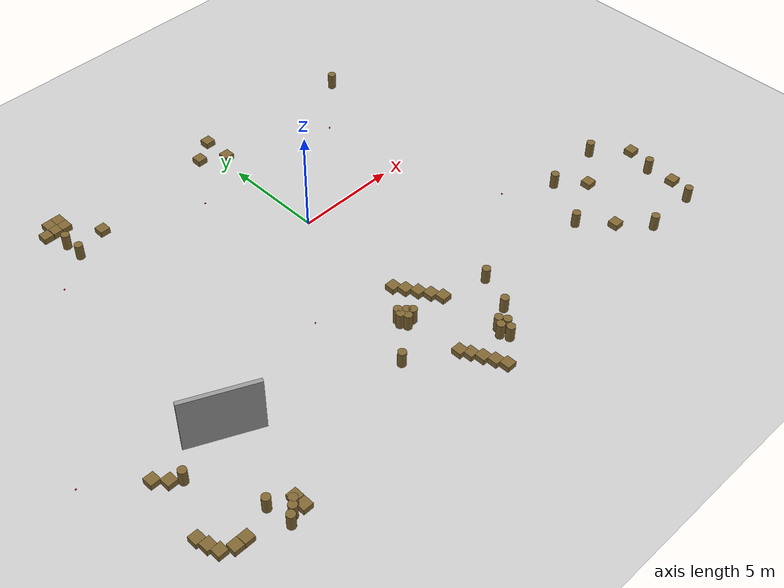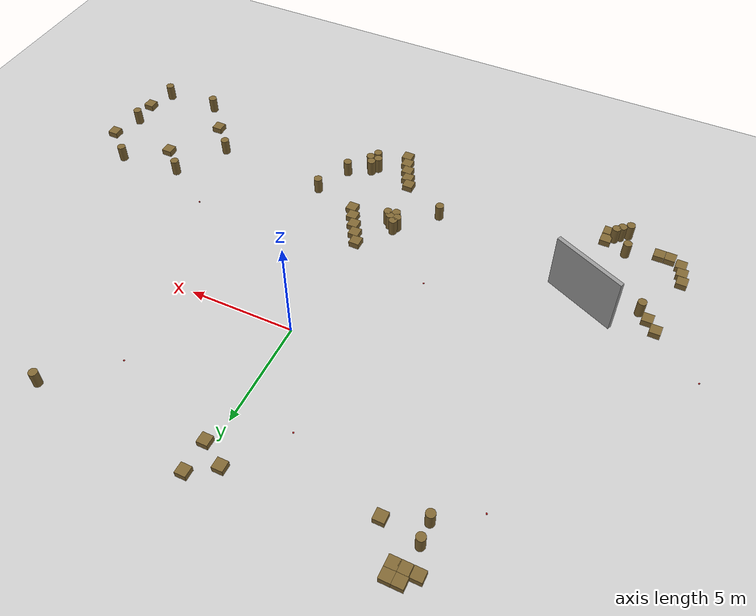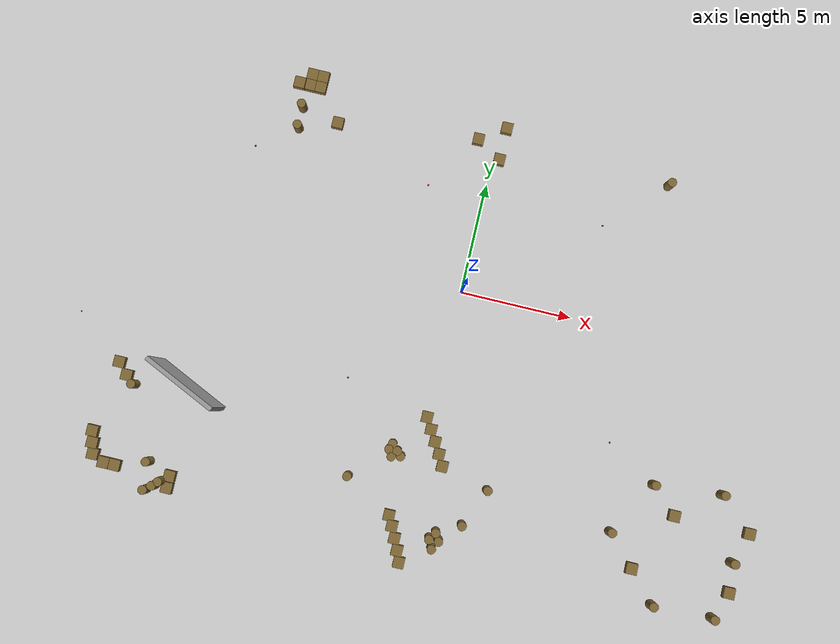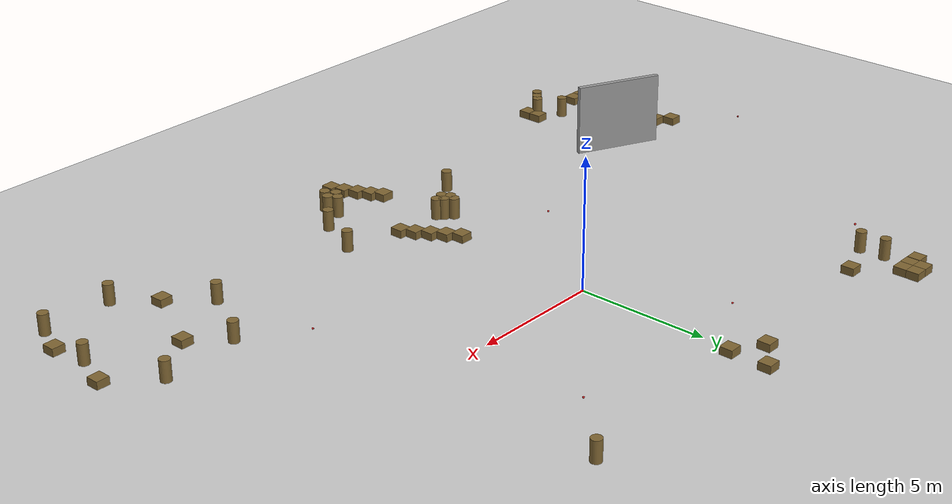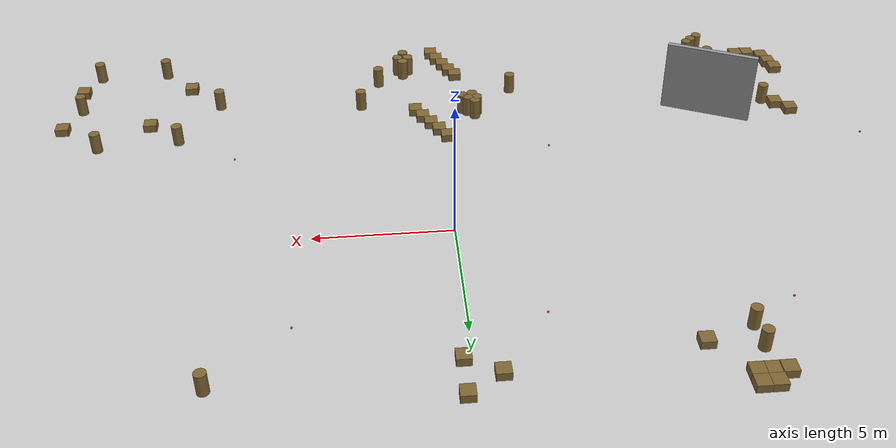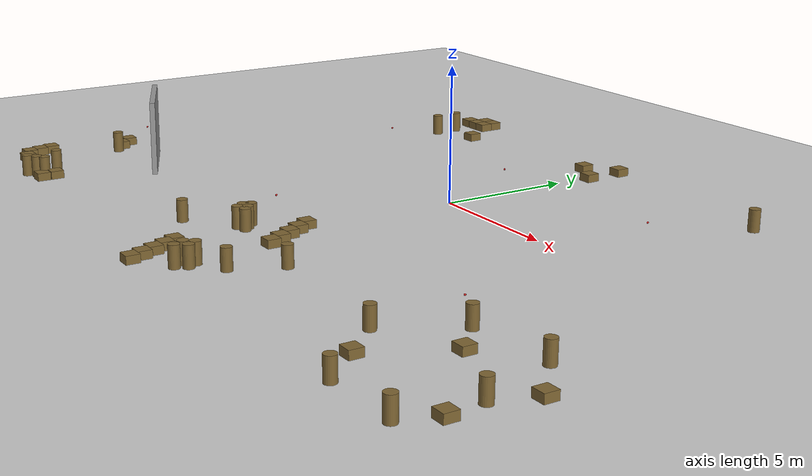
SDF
<sdf version="1.6">
 <world name="default">
  <scene><ambient>0.4 0.4 0.4 1</ambient><background>0.7 0.7 0.7 1</background><shadows>1</shadows></scene>
  <light name="sun" type="directional">
   <pose>0 0 10 0 -0 0</pose>
   <diffuse>0.8 0.8 0.8 1</diffuse>
   <specular>0.2 0.2 0.2 1</specular>
   <attenuation>
    <range>1000</range>
    <constant>0.9</constant>
    <linear>0.01</linear>
    <quadratic>0.001</quadratic>
   </attenuation>
   <direction>-0.5 0.1 -0.9</direction>
  </light>
  <model name="ground_plane">
   <static>1</static>
   <link name="link">
    <collision name="collision">
     <geometry><plane><normal>0 0 1</normal><size>100 100</size></plane></geometry>
     <surface><friction><ode><mu>100</mu><mu2>50</mu2></ode></friction></surface>
    </collision>
    <visual name="visual">
     <cast_shadows>0</cast_shadows>
     <geometry><plane><normal>0 0 1</normal><size>100 100</size></plane></geometry>
     <material>
      <script><uri>file://media/materials/scripts/gazebo.material</uri><name>Gazebo/Grey</name></script>
     </material>
    </visual>
   </link>
  </model>
  <physics name="default_physics" default="0" type="ode">
   <real_time_update_rate>1000</real_time_update_rate>
   <max_step_size>0.001</max_step_size>
   <real_time_factor>1</real_time_factor>
   <ode>
    <solver>
     <type>quick</type>
     <iters>150</iters>
     <precon_iters>0</precon_iters>
     <sor>1.4</sor>
     <use_dynamic_moi_rescaling>1</use_dynamic_moi_rescaling>
    </solver>
    <constraints>
     <cfm>1e-05</cfm>
     <erp>0.2</erp>
     <contact_max_correcting_vel>2000</contact_max_correcting_vel>
     <contact_surface_layer>0.01</contact_surface_layer>
    </constraints>
   </ode>
  </physics>
  <gravity>0 0 -9.8</gravity>
  <magnetic_field>6e-06 2.3e-05 -4.2e-05</magnetic_field>
  <atmosphere type="adiabatic"/>
  <spherical_coordinates>
   <surface_model>EARTH_WGS84</surface_model>
   <latitude_deg>0</latitude_deg>
   <longitude_deg>0</longitude_deg>
   <elevation>0</elevation>
   <heading_deg>0</heading_deg>
  </spherical_coordinates>
  <audio><device>default</device></audio>
  <model name="mini_cylinder_0_clone_0">
   <link name="link">
    <inertial>
     <mass>1</mass>
     <inertia><ixx>0.145833</ixx><ixy>0</ixy><ixz>0</ixz><iyy>0.145833</iyy><iyz>0</iyz><izz>0.125</izz></inertia>
    </inertial>
    <visual name="visual">
     <geometry><cylinder><radius>0.2</radius><length>0.8</length></cylinder></geometry>
     <material>
      <script><name>Gazebo/Grey</name><uri>file://media/materials/scripts/gazebo.material</uri></script>
      <shader type="vertex"><normal_map>__default__</normal_map></shader>
      <ambient>0.5 0.4 0.2 1</ambient>
      <diffuse>0.7 0.7 0.7 1</diffuse>
      <specular>0.01 0.01 0.01 1</specular>
      <emissive>0 0 0 1</emissive>
     </material>
    </visual>
    <collision name="collision">
     <geometry><cylinder><radius>0.2</radius><length>0.8</length></cylinder></geometry>
     <surface>
      <friction>
       <ode><mu>1</mu><mu2>1</mu2><fdir1>0 0 0</fdir1><slip1>0</slip1><slip2>0</slip2></ode>
       <torsional>
        <coefficient>1</coefficient>
        <patch_radius>0</patch_radius>
        <surface_radius>0</surface_radius>
        <use_patch_radius>1</use_patch_radius>
        <ode><slip>0</slip></ode>
       </torsional>
      </friction>
      <bounce><restitution_coefficient>0</restitution_coefficient><threshold>1e+06</threshold></bounce>
      <contact>
       <collide_without_contact>0</collide_without_contact>
       <collide_without_contact_bitmask>1</collide_without_contact_bitmask>
       <collide_bitmask>1</collide_bitmask>
       <ode>
        <soft_cfm>0</soft_cfm>
        <soft_erp>0.2</soft_erp>
        <kp>1e+13</kp>
        <kd>1</kd>
        <max_vel>0.01</max_vel>
        <min_depth>0</min_depth>
       </ode>
       <bullet>
        <split_impulse>1</split_impulse>
        <split_impulse_penetration_threshold>-0.01</split_impulse_penetration_threshold>
        <soft_cfm>0</soft_cfm>
        <soft_erp>0.2</soft_erp>
        <kp>1e+13</kp>
        <kd>1</kd>
       </bullet>
      </contact>
     </surface>
    </collision>
   </link>
   <static>1</static>
   <pose>8 6.85 0.4 0 -0 0</pose>
  </model>
  <model name="mini_box_clone_clone_0">
   <link name="link">
    <inertial>
     <mass>1</mass>
     <inertia>
      <ixx>0.166667</ixx>
      <ixy>0</ixy>
      <ixz>0</ixz>
      <iyy>0.166667</iyy>
      <iyz>0</iyz>
      <izz>0.166667</izz>
     </inertia>
    </inertial>
    <visual name="visual">
     <geometry><box><size>0.5 0.5 0.3</size></box></geometry>
     <material>
      <script><name>Gazebo/Grey</name><uri>file://media/materials/scripts/gazebo.material</uri></script>
      <shader type="vertex"><normal_map>__default__</normal_map></shader>
      <ambient>0.5 0.4 0.2 1</ambient>
      <diffuse>0.7 0.7 0.7 1</diffuse>
      <specular>0.01 0.01 0.01 1</specular>
      <emissive>0 0 0 1</emissive>
     </material>
    </visual>
    <collision name="collision">
     <geometry><box><size>0.5 0.5 0.3</size></box></geometry>
     <surface>
      <friction>
       <ode><mu>1</mu><mu2>1</mu2><fdir1>0 0 0</fdir1><slip1>0</slip1><slip2>0</slip2></ode>
       <torsional>
        <coefficient>1</coefficient>
        <patch_radius>0</patch_radius>
        <surface_radius>0</surface_radius>
        <use_patch_radius>1</use_patch_radius>
        <ode><slip>0</slip></ode>
       </torsional>
      </friction>
      <bounce><restitution_coefficient>0</restitution_coefficient><threshold>1e+06</threshold></bounce>
      <contact>
       <collide_without_contact>0</collide_without_contact>
       <collide_without_contact_bitmask>1</collide_without_contact_bitmask>
       <collide_bitmask>1</collide_bitmask>
       <ode>
        <soft_cfm>0</soft_cfm>
        <soft_erp>0.2</soft_erp>
        <kp>1e+13</kp>
        <kd>1</kd>
        <max_vel>0.01</max_vel>
        <min_depth>0</min_depth>
       </ode>
       <bullet>
        <split_impulse>1</split_impulse>
        <split_impulse_penetration_threshold>-0.01</split_impulse_penetration_threshold>
        <soft_cfm>0</soft_cfm>
        <soft_erp>0.2</soft_erp>
        <kp>1e+13</kp>
        <kd>1</kd>
       </bullet>
      </contact>
     </surface>
    </collision>
   </link>
   <static>1</static>
   <pose>0.311896 7.72531 0.15 0 -0 0</pose>
  </model>
  <model name="mini_box_clone_clone_2">
   <link name="link">
    <inertial>
     <mass>1</mass>
     <inertia>
      <ixx>0.166667</ixx>
      <ixy>0</ixy>
      <ixz>0</ixz>
      <iyy>0.166667</iyy>
      <iyz>0</iyz>
      <izz>0.166667</izz>
     </inertia>
    </inertial>
    <visual name="visual">
     <geometry><box><size>0.5 0.5 0.3</size></box></geometry>
     <material>
      <script><name>Gazebo/Grey</name><uri>file://media/materials/scripts/gazebo.material</uri></script>
      <shader type="vertex"><normal_map>__default__</normal_map></shader>
      <ambient>0.5 0.4 0.2 1</ambient>
      <diffuse>0.7 0.7 0.7 1</diffuse>
      <specular>0.01 0.01 0.01 1</specular>
      <emissive>0 0 0 1</emissive>
     </material>
    </visual>
    <collision name="collision">
     <geometry><box><size>0.5 0.5 0.3</size></box></geometry>
     <surface>
      <friction>
       <ode><mu>1</mu><mu2>1</mu2><fdir1>0 0 0</fdir1><slip1>0</slip1><slip2>0</slip2></ode>
       <torsional>
        <coefficient>1</coefficient>
        <patch_radius>0</patch_radius>
        <surface_radius>0</surface_radius>
        <use_patch_radius>1</use_patch_radius>
        <ode><slip>0</slip></ode>
       </torsional>
      </friction>
      <bounce><restitution_coefficient>0</restitution_coefficient><threshold>1e+06</threshold></bounce>
      <contact>
       <collide_without_contact>0</collide_without_contact>
       <collide_without_contact_bitmask>1</collide_without_contact_bitmask>
       <collide_bitmask>1</collide_bitmask>
       <ode>
        <soft_cfm>0</soft_cfm>
        <soft_erp>0.2</soft_erp>
        <kp>1e+13</kp>
        <kd>1</kd>
        <max_vel>0.01</max_vel>
        <min_depth>0</min_depth>
       </ode>
       <bullet>
        <split_impulse>1</split_impulse>
        <split_impulse_penetration_threshold>-0.01</split_impulse_penetration_threshold>
        <soft_cfm>0</soft_cfm>
        <soft_erp>0.2</soft_erp>
        <kp>1e+13</kp>
        <kd>1</kd>
       </bullet>
      </contact>
     </surface>
    </collision>
   </link>
   <static>1</static>
   <pose>-0.824684 6.94928 0.15 0 -0 0</pose>
  </model>
  <model name="mini_box_clone_clone_3">
   <link name="link">
    <inertial>
     <mass>1</mass>
     <inertia>
      <ixx>0.166667</ixx>
      <ixy>0</ixy>
      <ixz>0</ixz>
      <iyy>0.166667</iyy>
      <iyz>0</iyz>
      <izz>0.166667</izz>
     </inertia>
    </inertial>
    <visual name="visual">
     <geometry><box><size>0.5 0.5 0.3</size></box></geometry>
     <material>
      <script><name>Gazebo/Grey</name><uri>file://media/materials/scripts/gazebo.material</uri></script>
      <shader type="vertex"><normal_map>__default__</normal_map></shader>
      <ambient>0.5 0.4 0.2 1</ambient>
      <diffuse>0.7 0.7 0.7 1</diffuse>
      <specular>0.01 0.01 0.01 1</specular>
      <emissive>0 0 0 1</emissive>
     </material>
    </visual>
    <collision name="collision">
     <geometry><box><size>0.5 0.5 0.3</size></box></geometry>
     <surface>
      <friction>
       <ode><mu>1</mu><mu2>1</mu2><fdir1>0 0 0</fdir1><slip1>0</slip1><slip2>0</slip2></ode>
       <torsional>
        <coefficient>1</coefficient>
        <patch_radius>0</patch_radius>
        <surface_radius>0</surface_radius>
        <use_patch_radius>1</use_patch_radius>
        <ode><slip>0</slip></ode>
       </torsional>
      </friction>
      <bounce><restitution_coefficient>0</restitution_coefficient><threshold>1e+06</threshold></bounce>
      <contact>
       <collide_without_contact>0</collide_without_contact>
       <collide_without_contact_bitmask>1</collide_without_contact_bitmask>
       <collide_bitmask>1</collide_bitmask>
       <ode>
        <soft_cfm>0</soft_cfm>
        <soft_erp>0.2</soft_erp>
        <kp>1e+13</kp>
        <kd>1</kd>
        <max_vel>0.01</max_vel>
        <min_depth>0</min_depth>
       </ode>
       <bullet>
        <split_impulse>1</split_impulse>
        <split_impulse_penetration_threshold>-0.01</split_impulse_penetration_threshold>
        <soft_cfm>0</soft_cfm>
        <soft_erp>0.2</soft_erp>
        <kp>1e+13</kp>
        <kd>1</kd>
       </bullet>
      </contact>
     </surface>
    </collision>
   </link>
   <static>1</static>
   <pose>0.298756 6.25504 0.15 0 -0 0</pose>
  </model>
  <model name="mini_cylinder_0_clone_0_clone">
   <link name="link">
    <inertial>
     <mass>1</mass>
     <inertia><ixx>0.145833</ixx><ixy>0</ixy><ixz>0</ixz><iyy>0.145833</iyy><iyz>0</iyz><izz>0.125</izz></inertia>
    </inertial>
    <visual name="visual">
     <geometry><cylinder><radius>0.2</radius><length>0.8</length></cylinder></geometry>
     <material>
      <script><name>Gazebo/Grey</name><uri>file://media/materials/scripts/gazebo.material</uri></script>
      <shader type="vertex"><normal_map>__default__</normal_map></shader>
      <ambient>0.5 0.4 0.2 1</ambient>
      <diffuse>0.7 0.7 0.7 1</diffuse>
      <specular>0.01 0.01 0.01 1</specular>
      <emissive>0 0 0 1</emissive>
     </material>
    </visual>
    <collision name="collision">
     <geometry><cylinder><radius>0.2</radius><length>0.8</length></cylinder></geometry>
     <surface>
      <friction>
       <ode><mu>1</mu><mu2>1</mu2><fdir1>0 0 0</fdir1><slip1>0</slip1><slip2>0</slip2></ode>
       <torsional>
        <coefficient>1</coefficient>
        <patch_radius>0</patch_radius>
        <surface_radius>0</surface_radius>
        <use_patch_radius>1</use_patch_radius>
        <ode><slip>0</slip></ode>
       </torsional>
      </friction>
      <bounce><restitution_coefficient>0</restitution_coefficient><threshold>1e+06</threshold></bounce>
      <contact>
       <collide_without_contact>0</collide_without_contact>
       <collide_without_contact_bitmask>1</collide_without_contact_bitmask>
       <collide_bitmask>1</collide_bitmask>
       <ode>
        <soft_cfm>0</soft_cfm>
        <soft_erp>0.2</soft_erp>
        <kp>1e+13</kp>
        <kd>1</kd>
        <max_vel>0.01</max_vel>
        <min_depth>0</min_depth>
       </ode>
       <bullet>
        <split_impulse>1</split_impulse>
        <split_impulse_penetration_threshold>-0.01</split_impulse_penetration_threshold>
        <soft_cfm>0</soft_cfm>
        <soft_erp>0.2</soft_erp>
        <kp>1e+13</kp>
        <kd>1</kd>
       </bullet>
      </contact>
     </surface>
    </collision>
   </link>
   <static>1</static>
   <pose>13.224 -6.11998 0.4 0 -0 0</pose>
  </model>
  <model name="mini_cylinder_0_clone_0_clone_0">
   <link name="link">
    <inertial>
     <mass>1</mass>
     <inertia><ixx>0.145833</ixx><ixy>0</ixy><ixz>0</ixz><iyy>0.145833</iyy><iyz>0</iyz><izz>0.125</izz></inertia>
    </inertial>
    <visual name="visual">
     <geometry><cylinder><radius>0.2</radius><length>0.8</length></cylinder></geometry>
     <material>
      <script><name>Gazebo/Grey</name><uri>file://media/materials/scripts/gazebo.material</uri></script>
      <shader type="vertex"><normal_map>__default__</normal_map></shader>
      <ambient>0.5 0.4 0.2 1</ambient>
      <diffuse>0.7 0.7 0.7 1</diffuse>
      <specular>0.01 0.01 0.01 1</specular>
      <emissive>0 0 0 1</emissive>
     </material>
    </visual>
    <collision name="collision">
     <geometry><cylinder><radius>0.2</radius><length>0.8</length></cylinder></geometry>
     <surface>
      <friction>
       <ode><mu>1</mu><mu2>1</mu2><fdir1>0 0 0</fdir1><slip1>0</slip1><slip2>0</slip2></ode>
       <torsional>
        <coefficient>1</coefficient>
        <patch_radius>0</patch_radius>
        <surface_radius>0</surface_radius>
        <use_patch_radius>1</use_patch_radius>
        <ode><slip>0</slip></ode>
       </torsional>
      </friction>
      <bounce><restitution_coefficient>0</restitution_coefficient><threshold>1e+06</threshold></bounce>
      <contact>
       <collide_without_contact>0</collide_without_contact>
       <collide_without_contact_bitmask>1</collide_without_contact_bitmask>
       <collide_bitmask>1</collide_bitmask>
       <ode>
        <soft_cfm>0</soft_cfm>
        <soft_erp>0.2</soft_erp>
        <kp>1e+13</kp>
        <kd>1</kd>
        <max_vel>0.01</max_vel>
        <min_depth>0</min_depth>
       </ode>
       <bullet>
        <split_impulse>1</split_impulse>
        <split_impulse_penetration_threshold>-0.01</split_impulse_penetration_threshold>
        <soft_cfm>0</soft_cfm>
        <soft_erp>0.2</soft_erp>
        <kp>1e+13</kp>
        <kd>1</kd>
       </bullet>
      </contact>
     </surface>
    </collision>
   </link>
   <static>1</static>
   <pose>8.7545 -8.82263 0.4 0 -0 0</pose>
  </model>
  <model name="mini_cylinder_0_clone_0_clone_1">
   <link name="link">
    <inertial>
     <mass>1</mass>
     <inertia><ixx>0.145833</ixx><ixy>0</ixy><ixz>0</ixz><iyy>0.145833</iyy><iyz>0</iyz><izz>0.125</izz></inertia>
    </inertial>
    <visual name="visual">
     <geometry><cylinder><radius>0.2</radius><length>0.8</length></cylinder></geometry>
     <material>
      <script><name>Gazebo/Grey</name><uri>file://media/materials/scripts/gazebo.material</uri></script>
      <shader type="vertex"><normal_map>__default__</normal_map></shader>
      <ambient>0.5 0.4 0.2 1</ambient>
      <diffuse>0.7 0.7 0.7 1</diffuse>
      <specular>0.01 0.01 0.01 1</specular>
      <emissive>0 0 0 1</emissive>
     </material>
    </visual>
    <collision name="collision">
     <geometry><cylinder><radius>0.2</radius><length>0.8</length></cylinder></geometry>
     <surface>
      <friction>
       <ode><mu>1</mu><mu2>1</mu2><fdir1>0 0 0</fdir1><slip1>0</slip1><slip2>0</slip2></ode>
       <torsional>
        <coefficient>1</coefficient>
        <patch_radius>0</patch_radius>
        <surface_radius>0</surface_radius>
        <use_patch_radius>1</use_patch_radius>
        <ode><slip>0</slip></ode>
       </torsional>
      </friction>
      <bounce><restitution_coefficient>0</restitution_coefficient><threshold>1e+06</threshold></bounce>
      <contact>
       <collide_without_contact>0</collide_without_contact>
       <collide_without_contact_bitmask>1</collide_without_contact_bitmask>
       <collide_bitmask>1</collide_bitmask>
       <ode>
        <soft_cfm>0</soft_cfm>
        <soft_erp>0.2</soft_erp>
        <kp>1e+13</kp>
        <kd>1</kd>
        <max_vel>0.01</max_vel>
        <min_depth>0</min_depth>
       </ode>
       <bullet>
        <split_impulse>1</split_impulse>
        <split_impulse_penetration_threshold>-0.01</split_impulse_penetration_threshold>
        <soft_cfm>0</soft_cfm>
        <soft_erp>0.2</soft_erp>
        <kp>1e+13</kp>
        <kd>1</kd>
       </bullet>
      </contact>
     </surface>
    </collision>
   </link>
   <static>1</static>
   <pose>14.2436 -8.91515 0.4 0 -0 0</pose>
  </model>
  <model name="mini_cylinder_0_clone_0_clone_2">
   <link name="link">
    <inertial>
     <mass>1</mass>
     <inertia><ixx>0.145833</ixx><ixy>0</ixy><ixz>0</ixz><iyy>0.145833</iyy><iyz>0</iyz><izz>0.125</izz></inertia>
    </inertial>
    <visual name="visual">
     <geometry><cylinder><radius>0.2</radius><length>0.8</length></cylinder></geometry>
     <material>
      <script><name>Gazebo/Grey</name><uri>file://media/materials/scripts/gazebo.material</uri></script>
      <shader type="vertex"><normal_map>__default__</normal_map></shader>
      <ambient>0.5 0.4 0.2 1</ambient>
      <diffuse>0.7 0.7 0.7 1</diffuse>
      <specular>0.01 0.01 0.01 1</specular>
      <emissive>0 0 0 1</emissive>
     </material>
    </visual>
    <collision name="collision">
     <geometry><cylinder><radius>0.2</radius><length>0.8</length></cylinder></geometry>
     <surface>
      <friction>
       <ode><mu>1</mu><mu2>1</mu2><fdir1>0 0 0</fdir1><slip1>0</slip1><slip2>0</slip2></ode>
       <torsional>
        <coefficient>1</coefficient>
        <patch_radius>0</patch_radius>
        <surface_radius>0</surface_radius>
        <use_patch_radius>1</use_patch_radius>
        <ode><slip>0</slip></ode>
       </torsional>
      </friction>
      <bounce><restitution_coefficient>0</restitution_coefficient><threshold>1e+06</threshold></bounce>
      <contact>
       <collide_without_contact>0</collide_without_contact>
       <collide_without_contact_bitmask>1</collide_without_contact_bitmask>
       <collide_bitmask>1</collide_bitmask>
       <ode>
        <soft_cfm>0</soft_cfm>
        <soft_erp>0.2</soft_erp>
        <kp>1e+13</kp>
        <kd>1</kd>
        <max_vel>0.01</max_vel>
        <min_depth>0</min_depth>
       </ode>
       <bullet>
        <split_impulse>1</split_impulse>
        <split_impulse_penetration_threshold>-0.01</split_impulse_penetration_threshold>
        <soft_cfm>0</soft_cfm>
        <soft_erp>0.2</soft_erp>
        <kp>1e+13</kp>
        <kd>1</kd>
       </bullet>
      </contact>
     </surface>
    </collision>
   </link>
   <static>1</static>
   <pose>13.8924 -11.4476 0.4 0 -0 0</pose>
  </model>
  <model name="mini_box_clone_clone_3_clone">
   <link name="link">
    <inertial>
     <mass>1</mass>
     <inertia>
      <ixx>0.166667</ixx>
      <ixy>0</ixy>
      <ixz>0</ixz>
      <iyy>0.166667</iyy>
      <iyz>0</iyz>
      <izz>0.166667</izz>
     </inertia>
    </inertial>
    <visual name="visual">
     <geometry><box><size>0.5 0.5 0.3</size></box></geometry>
     <material>
      <script><name>Gazebo/Grey</name><uri>file://media/materials/scripts/gazebo.material</uri></script>
      <shader type="vertex"><normal_map>__default__</normal_map></shader>
      <ambient>0.5 0.4 0.2 1</ambient>
      <diffuse>0.7 0.7 0.7 1</diffuse>
      <specular>0.01 0.01 0.01 1</specular>
      <emissive>0 0 0 1</emissive>
     </material>
    </visual>
    <collision name="collision">
     <geometry><box><size>0.5 0.5 0.3</size></box></geometry>
     <surface>
      <friction>
       <ode><mu>1</mu><mu2>1</mu2><fdir1>0 0 0</fdir1><slip1>0</slip1><slip2>0</slip2></ode>
       <torsional>
        <coefficient>1</coefficient>
        <patch_radius>0</patch_radius>
        <surface_radius>0</surface_radius>
        <use_patch_radius>1</use_patch_radius>
        <ode><slip>0</slip></ode>
       </torsional>
      </friction>
      <bounce><restitution_coefficient>0</restitution_coefficient><threshold>1e+06</threshold></bounce>
      <contact>
       <collide_without_contact>0</collide_without_contact>
       <collide_without_contact_bitmask>1</collide_without_contact_bitmask>
       <collide_bitmask>1</collide_bitmask>
       <ode>
        <soft_cfm>0</soft_cfm>
        <soft_erp>0.2</soft_erp>
        <kp>1e+13</kp>
        <kd>1</kd>
        <max_vel>0.01</max_vel>
        <min_depth>0</min_depth>
       </ode>
       <bullet>
        <split_impulse>1</split_impulse>
        <split_impulse_penetration_threshold>-0.01</split_impulse_penetration_threshold>
        <soft_cfm>0</soft_cfm>
        <soft_erp>0.2</soft_erp>
        <kp>1e+13</kp>
        <kd>1</kd>
       </bullet>
      </contact>
     </surface>
    </collision>
   </link>
   <static>1</static>
   <pose>11.3808 -7.50629 0.15 0 -0 0</pose>
  </model>
  <model name="mini_box_clone_clone_3_clone_0">
   <link name="link">
    <inertial>
     <mass>1</mass>
     <inertia>
      <ixx>0.166667</ixx>
      <ixy>0</ixy>
      <ixz>0</ixz>
      <iyy>0.166667</iyy>
      <iyz>0</iyz>
      <izz>0.166667</izz>
     </inertia>
    </inertial>
    <visual name="visual">
     <geometry><box><size>0.5 0.5 0.3</size></box></geometry>
     <material>
      <script><name>Gazebo/Grey</name><uri>file://media/materials/scripts/gazebo.material</uri></script>
      <shader type="vertex"><normal_map>__default__</normal_map></shader>
      <ambient>0.5 0.4 0.2 1</ambient>
      <diffuse>0.7 0.7 0.7 1</diffuse>
      <specular>0.01 0.01 0.01 1</specular>
      <emissive>0 0 0 1</emissive>
     </material>
    </visual>
    <collision name="collision">
     <geometry><box><size>0.5 0.5 0.3</size></box></geometry>
     <surface>
      <friction>
       <ode><mu>1</mu><mu2>1</mu2><fdir1>0 0 0</fdir1><slip1>0</slip1><slip2>0</slip2></ode>
       <torsional>
        <coefficient>1</coefficient>
        <patch_radius>0</patch_radius>
        <surface_radius>0</surface_radius>
        <use_patch_radius>1</use_patch_radius>
        <ode><slip>0</slip></ode>
       </torsional>
      </friction>
      <bounce><restitution_coefficient>0</restitution_coefficient><threshold>1e+06</threshold></bounce>
      <contact>
       <collide_without_contact>0</collide_without_contact>
       <collide_without_contact_bitmask>1</collide_without_contact_bitmask>
       <collide_bitmask>1</collide_bitmask>
       <ode>
        <soft_cfm>0</soft_cfm>
        <soft_erp>0.2</soft_erp>
        <kp>1e+13</kp>
        <kd>1</kd>
        <max_vel>0.01</max_vel>
        <min_depth>0</min_depth>
       </ode>
       <bullet>
        <split_impulse>1</split_impulse>
        <split_impulse_penetration_threshold>-0.01</split_impulse_penetration_threshold>
        <soft_cfm>0</soft_cfm>
        <soft_erp>0.2</soft_erp>
        <kp>1e+13</kp>
        <kd>1</kd>
       </bullet>
      </contact>
     </surface>
    </collision>
   </link>
   <static>1</static>
   <pose>10.0339 -10.1728 0.15 0 -0 0</pose>
  </model>
  <model name="mini_box_clone_clone_3_clone_1">
   <link name="link">
    <inertial>
     <mass>1</mass>
     <inertia>
      <ixx>0.166667</ixx>
      <ixy>0</ixy>
      <ixz>0</ixz>
      <iyy>0.166667</iyy>
      <iyz>0</iyz>
      <izz>0.166667</izz>
     </inertia>
    </inertial>
    <visual name="visual">
     <geometry><box><size>0.5 0.5 0.3</size></box></geometry>
     <material>
      <script><name>Gazebo/Grey</name><uri>file://media/materials/scripts/gazebo.material</uri></script>
      <shader type="vertex"><normal_map>__default__</normal_map></shader>
      <ambient>0.5 0.4 0.2 1</ambient>
      <diffuse>0.7 0.7 0.7 1</diffuse>
      <specular>0.01 0.01 0.01 1</specular>
      <emissive>0 0 0 1</emissive>
     </material>
    </visual>
    <collision name="collision">
     <geometry><box><size>0.5 0.5 0.3</size></box></geometry>
     <surface>
      <friction>
       <ode><mu>1</mu><mu2>1</mu2><fdir1>0 0 0</fdir1><slip1>0</slip1><slip2>0</slip2></ode>
       <torsional>
        <coefficient>1</coefficient>
        <patch_radius>0</patch_radius>
        <surface_radius>0</surface_radius>
        <use_patch_radius>1</use_patch_radius>
        <ode><slip>0</slip></ode>
       </torsional>
      </friction>
      <bounce><restitution_coefficient>0</restitution_coefficient><threshold>1e+06</threshold></bounce>
      <contact>
       <collide_without_contact>0</collide_without_contact>
       <collide_without_contact_bitmask>1</collide_without_contact_bitmask>
       <collide_bitmask>1</collide_bitmask>
       <ode>
        <soft_cfm>0</soft_cfm>
        <soft_erp>0.2</soft_erp>
        <kp>1e+13</kp>
        <kd>1</kd>
        <max_vel>0.01</max_vel>
        <min_depth>0</min_depth>
       </ode>
       <bullet>
        <split_impulse>1</split_impulse>
        <split_impulse_penetration_threshold>-0.01</split_impulse_penetration_threshold>
        <soft_cfm>0</soft_cfm>
        <soft_erp>0.2</soft_erp>
        <kp>1e+13</kp>
        <kd>1</kd>
       </bullet>
      </contact>
     </surface>
    </collision>
   </link>
   <static>1</static>
   <pose>14.4187 -10.2264 0.15 0 -0 0</pose>
  </model>
  <model name="mini_box_clone_clone_3_clone_2">
   <link name="link">
    <inertial>
     <mass>1</mass>
     <inertia>
      <ixx>0.166667</ixx>
      <ixy>0</ixy>
      <ixz>0</ixz>
      <iyy>0.166667</iyy>
      <iyz>0</iyz>
      <izz>0.166667</izz>
     </inertia>
    </inertial>
    <visual name="visual">
     <geometry><box><size>0.5 0.5 0.3</size></box></geometry>
     <material>
      <script><name>Gazebo/Grey</name><uri>file://media/materials/scripts/gazebo.material</uri></script>
      <shader type="vertex"><normal_map>__default__</normal_map></shader>
      <ambient>0.5 0.4 0.2 1</ambient>
      <diffuse>0.7 0.7 0.7 1</diffuse>
      <specular>0.01 0.01 0.01 1</specular>
      <emissive>0 0 0 1</emissive>
     </material>
    </visual>
    <collision name="collision">
     <geometry><box><size>0.5 0.5 0.3</size></box></geometry>
     <surface>
      <friction>
       <ode><mu>1</mu><mu2>1</mu2><fdir1>0 0 0</fdir1><slip1>0</slip1><slip2>0</slip2></ode>
       <torsional>
        <coefficient>1</coefficient>
        <patch_radius>0</patch_radius>
        <surface_radius>0</surface_radius>
        <use_patch_radius>1</use_patch_radius>
        <ode><slip>0</slip></ode>
       </torsional>
      </friction>
      <bounce><restitution_coefficient>0</restitution_coefficient><threshold>1e+06</threshold></bounce>
      <contact>
       <collide_without_contact>0</collide_without_contact>
       <collide_without_contact_bitmask>1</collide_without_contact_bitmask>
       <collide_bitmask>1</collide_bitmask>
       <ode>
        <soft_cfm>0</soft_cfm>
        <soft_erp>0.2</soft_erp>
        <kp>1e+13</kp>
        <kd>1</kd>
        <max_vel>0.01</max_vel>
        <min_depth>0</min_depth>
       </ode>
       <bullet>
        <split_impulse>1</split_impulse>
        <split_impulse_penetration_threshold>-0.01</split_impulse_penetration_threshold>
        <soft_cfm>0</soft_cfm>
        <soft_erp>0.2</soft_erp>
        <kp>1e+13</kp>
        <kd>1</kd>
       </bullet>
      </contact>
     </surface>
    </collision>
   </link>
   <static>1</static>
   <pose>14.767 -7.51176 0.15 0 -0 0</pose>
  </model>
  <model name="mini_cylinder_0_clone_0_clone_clone">
   <link name="link">
    <inertial>
     <mass>1</mass>
     <inertia><ixx>0.145833</ixx><ixy>0</ixy><ixz>0</ixz><iyy>0.145833</iyy><iyz>0</iyz><izz>0.125</izz></inertia>
    </inertial>
    <visual name="visual">
     <geometry><cylinder><radius>0.2</radius><length>0.8</length></cylinder></geometry>
     <material>
      <script><name>Gazebo/Grey</name><uri>file://media/materials/scripts/gazebo.material</uri></script>
      <shader type="vertex"><normal_map>__default__</normal_map></shader>
      <ambient>0.5 0.4 0.2 1</ambient>
      <diffuse>0.7 0.7 0.7 1</diffuse>
      <specular>0.01 0.01 0.01 1</specular>
      <emissive>0 0 0 1</emissive>
     </material>
    </visual>
    <collision name="collision">
     <geometry><cylinder><radius>0.2</radius><length>0.8</length></cylinder></geometry>
     <surface>
      <friction>
       <ode><mu>1</mu><mu2>1</mu2><fdir1>0 0 0</fdir1><slip1>0</slip1><slip2>0</slip2></ode>
       <torsional>
        <coefficient>1</coefficient>
        <patch_radius>0</patch_radius>
        <surface_radius>0</surface_radius>
        <use_patch_radius>1</use_patch_radius>
        <ode><slip>0</slip></ode>
       </torsional>
      </friction>
      <bounce><restitution_coefficient>0</restitution_coefficient><threshold>1e+06</threshold></bounce>
      <contact>
       <collide_without_contact>0</collide_without_contact>
       <collide_without_contact_bitmask>1</collide_without_contact_bitmask>
       <collide_bitmask>1</collide_bitmask>
       <ode>
        <soft_cfm>0</soft_cfm>
        <soft_erp>0.2</soft_erp>
        <kp>1e+13</kp>
        <kd>1</kd>
        <max_vel>0.01</max_vel>
        <min_depth>0</min_depth>
       </ode>
       <bullet>
        <split_impulse>1</split_impulse>
        <split_impulse_penetration_threshold>-0.01</split_impulse_penetration_threshold>
        <soft_cfm>0</soft_cfm>
        <soft_erp>0.2</soft_erp>
        <kp>1e+13</kp>
        <kd>1</kd>
       </bullet>
      </contact>
     </surface>
    </collision>
   </link>
   <static>1</static>
   <pose>10.1744 -6.38296 0.4 0 -0 0</pose>
  </model>
  <model name="mini_cylinder_0_clone_0_clone_clone_0">
   <link name="link">
    <inertial>
     <mass>1</mass>
     <inertia><ixx>0.145833</ixx><ixy>0</ixy><ixz>0</ixz><iyy>0.145833</iyy><iyz>0</iyz><izz>0.125</izz></inertia>
    </inertial>
    <visual name="visual">
     <geometry><cylinder><radius>0.2</radius><length>0.8</length></cylinder></geometry>
     <material>
      <script><name>Gazebo/Grey</name><uri>file://media/materials/scripts/gazebo.material</uri></script>
      <shader type="vertex"><normal_map>__default__</normal_map></shader>
      <ambient>0.5 0.4 0.2 1</ambient>
      <diffuse>0.7 0.7 0.7 1</diffuse>
      <specular>0.01 0.01 0.01 1</specular>
      <emissive>0 0 0 1</emissive>
     </material>
    </visual>
    <collision name="collision">
     <geometry><cylinder><radius>0.2</radius><length>0.8</length></cylinder></geometry>
     <surface>
      <friction>
       <ode><mu>1</mu><mu2>1</mu2><fdir1>0 0 0</fdir1><slip1>0</slip1><slip2>0</slip2></ode>
       <torsional>
        <coefficient>1</coefficient>
        <patch_radius>0</patch_radius>
        <surface_radius>0</surface_radius>
        <use_patch_radius>1</use_patch_radius>
        <ode><slip>0</slip></ode>
       </torsional>
      </friction>
      <bounce><restitution_coefficient>0</restitution_coefficient><threshold>1e+06</threshold></bounce>
      <contact>
       <collide_without_contact>0</collide_without_contact>
       <collide_without_contact_bitmask>1</collide_without_contact_bitmask>
       <collide_bitmask>1</collide_bitmask>
       <ode>
        <soft_cfm>0</soft_cfm>
        <soft_erp>0.2</soft_erp>
        <kp>1e+13</kp>
        <kd>1</kd>
        <max_vel>0.01</max_vel>
        <min_depth>0</min_depth>
       </ode>
       <bullet>
        <split_impulse>1</split_impulse>
        <split_impulse_penetration_threshold>-0.01</split_impulse_penetration_threshold>
        <soft_cfm>0</soft_cfm>
        <soft_erp>0.2</soft_erp>
        <kp>1e+13</kp>
        <kd>1</kd>
       </bullet>
      </contact>
     </surface>
    </collision>
   </link>
   <static>1</static>
   <pose>11.1967 -11.5076 0.4 0 -0 0</pose>
  </model>
  <model name="grey_wall_3.5">
   <link name="link">
    <pose>0 0 1.4 0 -0 0</pose>
    <inertial>
     <mass>1</mass>
     <inertia><ixx>1</ixx><ixy>0</ixy><ixz>0</ixz><iyy>1</iyy><iyz>0</iyz><izz>1</izz></inertia>
    </inertial>
    <visual name="visual">
     <cast_shadows>0</cast_shadows>
     <geometry><box><size>3.5 0.2 2.8</size></box></geometry>
     <material>
      <script>
       <uri>model://grey_wall/materials/scripts</uri>
       <uri>model://grey_wall/materials/textures</uri>
       <name>vrc/grey_wall</name>
      </script>
      <shader type="vertex"><normal_map>__default__</normal_map></shader>
      <ambient>1 1 1 1</ambient>
      <diffuse>1 1 1 1</diffuse>
      <specular>0 0 0 1</specular>
      <emissive>0 0 0 1</emissive>
     </material>
    </visual>
    <collision name="collision">
     <geometry><box><size>3.5 0.2 2.8</size></box></geometry>
     <surface>
      <friction>
       <ode><mu>1</mu><mu2>1</mu2><fdir1>0 0 0</fdir1><slip1>0</slip1><slip2>0</slip2></ode>
       <torsional>
        <coefficient>1</coefficient>
        <patch_radius>0</patch_radius>
        <surface_radius>0</surface_radius>
        <use_patch_radius>1</use_patch_radius>
        <ode><slip>0</slip></ode>
       </torsional>
      </friction>
      <bounce><restitution_coefficient>0</restitution_coefficient><threshold>1e+06</threshold></bounce>
      <contact>
       <collide_without_contact>0</collide_without_contact>
       <collide_without_contact_bitmask>1</collide_without_contact_bitmask>
       <collide_bitmask>1</collide_bitmask>
       <ode>
        <soft_cfm>0</soft_cfm>
        <soft_erp>0.2</soft_erp>
        <kp>1e+13</kp>
        <kd>1</kd>
        <max_vel>0.01</max_vel>
        <min_depth>0</min_depth>
       </ode>
       <bullet>
        <split_impulse>1</split_impulse>
        <split_impulse_penetration_threshold>-0.01</split_impulse_penetration_threshold>
        <soft_cfm>0</soft_cfm>
        <soft_erp>0.2</soft_erp>
        <kp>1e+13</kp>
        <kd>1</kd>
       </bullet>
      </contact>
     </surface>
    </collision>
   </link>
   <static>1</static>
   <pose>-10.6984 -6.76515 0 0 0 -0.436121</pose>
  </model>
  <model name="mini_box_clone_clone_2_clone">
   <link name="link">
    <inertial>
     <mass>1</mass>
     <inertia>
      <ixx>0.166667</ixx>
      <ixy>0</ixy>
      <ixz>0</ixz>
      <iyy>0.166667</iyy>
      <iyz>0</iyz>
      <izz>0.166667</izz>
     </inertia>
    </inertial>
    <visual name="visual">
     <geometry><box><size>0.5 0.5 0.3</size></box></geometry>
     <material>
      <script><name>Gazebo/Grey</name><uri>file://media/materials/scripts/gazebo.material</uri></script>
      <shader type="vertex"><normal_map>__default__</normal_map></shader>
      <ambient>0.5 0.4 0.2 1</ambient>
      <diffuse>0.7 0.7 0.7 1</diffuse>
      <specular>0.01 0.01 0.01 1</specular>
      <emissive>0 0 0 1</emissive>
     </material>
    </visual>
    <collision name="collision">
     <geometry><box><size>0.5 0.5 0.3</size></box></geometry>
     <surface>
      <friction>
       <ode><mu>1</mu><mu2>1</mu2><fdir1>0 0 0</fdir1><slip1>0</slip1><slip2>0</slip2></ode>
       <torsional>
        <coefficient>1</coefficient>
        <patch_radius>0</patch_radius>
        <surface_radius>0</surface_radius>
        <use_patch_radius>1</use_patch_radius>
        <ode><slip>0</slip></ode>
       </torsional>
      </friction>
      <bounce><restitution_coefficient>0</restitution_coefficient><threshold>1e+06</threshold></bounce>
      <contact>
       <collide_without_contact>0</collide_without_contact>
       <collide_without_contact_bitmask>1</collide_without_contact_bitmask>
       <collide_bitmask>1</collide_bitmask>
       <ode>
        <soft_cfm>0</soft_cfm>
        <soft_erp>0.2</soft_erp>
        <kp>1e+13</kp>
        <kd>1</kd>
        <max_vel>0.01</max_vel>
        <min_depth>0</min_depth>
       </ode>
       <bullet>
        <split_impulse>1</split_impulse>
        <split_impulse_penetration_threshold>-0.01</split_impulse_penetration_threshold>
        <soft_cfm>0</soft_cfm>
        <soft_erp>0.2</soft_erp>
        <kp>1e+13</kp>
        <kd>1</kd>
       </bullet>
      </contact>
     </surface>
    </collision>
   </link>
   <static>1</static>
   <pose>-7.18928 6.21457 0.15 0 -0 0</pose>
  </model>
  <model name="mini_cylinder_0_clone_0_clone_3">
   <link name="link">
    <inertial>
     <mass>1</mass>
     <inertia><ixx>0.145833</ixx><ixy>0</ixy><ixz>0</ixz><iyy>0.145833</iyy><iyz>0</iyz><izz>0.125</izz></inertia>
    </inertial>
    <visual name="visual">
     <geometry><cylinder><radius>0.2</radius><length>0.8</length></cylinder></geometry>
     <material>
      <script><name>Gazebo/Grey</name><uri>file://media/materials/scripts/gazebo.material</uri></script>
      <shader type="vertex"><normal_map>__default__</normal_map></shader>
      <ambient>0.5 0.4 0.2 1</ambient>
      <diffuse>0.7 0.7 0.7 1</diffuse>
      <specular>0.01 0.01 0.01 1</specular>
      <emissive>0 0 0 1</emissive>
     </material>
    </visual>
    <collision name="collision">
     <geometry><cylinder><radius>0.2</radius><length>0.8</length></cylinder></geometry>
     <surface>
      <friction>
       <ode><mu>1</mu><mu2>1</mu2><fdir1>0 0 0</fdir1><slip1>0</slip1><slip2>0</slip2></ode>
       <torsional>
        <coefficient>1</coefficient>
        <patch_radius>0</patch_radius>
        <surface_radius>0</surface_radius>
        <use_patch_radius>1</use_patch_radius>
        <ode><slip>0</slip></ode>
       </torsional>
      </friction>
      <bounce><restitution_coefficient>0</restitution_coefficient><threshold>1e+06</threshold></bounce>
      <contact>
       <collide_without_contact>0</collide_without_contact>
       <collide_without_contact_bitmask>1</collide_without_contact_bitmask>
       <collide_bitmask>1</collide_bitmask>
       <ode>
        <soft_cfm>0</soft_cfm>
        <soft_erp>0.2</soft_erp>
        <kp>1e+13</kp>
        <kd>1</kd>
        <max_vel>0.01</max_vel>
        <min_depth>0</min_depth>
       </ode>
       <bullet>
        <split_impulse>1</split_impulse>
        <split_impulse_penetration_threshold>-0.01</split_impulse_penetration_threshold>
        <soft_cfm>0</soft_cfm>
        <soft_erp>0.2</soft_erp>
        <kp>1e+13</kp>
        <kd>1</kd>
       </bullet>
      </contact>
     </surface>
    </collision>
   </link>
   <static>1</static>
   <pose>-8.90855 6.55503 0.4 0 -0 0</pose>
  </model>
  <model name="mini_cylinder_0_clone_0_clone_4">
   <link name="link">
    <inertial>
     <mass>1</mass>
     <inertia><ixx>0.145833</ixx><ixy>0</ixy><ixz>0</ixz><iyy>0.145833</iyy><iyz>0</iyz><izz>0.125</izz></inertia>
    </inertial>
    <visual name="visual">
     <geometry><cylinder><radius>0.2</radius><length>0.8</length></cylinder></geometry>
     <material>
      <script><name>Gazebo/Grey</name><uri>file://media/materials/scripts/gazebo.material</uri></script>
      <shader type="vertex"><normal_map>__default__</normal_map></shader>
      <ambient>0.5 0.4 0.2 1</ambient>
      <diffuse>0.7 0.7 0.7 1</diffuse>
      <specular>0.01 0.01 0.01 1</specular>
      <emissive>0 0 0 1</emissive>
     </material>
    </visual>
    <collision name="collision">
     <geometry><cylinder><radius>0.2</radius><length>0.8</length></cylinder></geometry>
     <surface>
      <friction>
       <ode><mu>1</mu><mu2>1</mu2><fdir1>0 0 0</fdir1><slip1>0</slip1><slip2>0</slip2></ode>
       <torsional>
        <coefficient>1</coefficient>
        <patch_radius>0</patch_radius>
        <surface_radius>0</surface_radius>
        <use_patch_radius>1</use_patch_radius>
        <ode><slip>0</slip></ode>
       </torsional>
      </friction>
      <bounce><restitution_coefficient>0</restitution_coefficient><threshold>1e+06</threshold></bounce>
      <contact>
       <collide_without_contact>0</collide_without_contact>
       <collide_without_contact_bitmask>1</collide_without_contact_bitmask>
       <collide_bitmask>1</collide_bitmask>
       <ode>
        <soft_cfm>0</soft_cfm>
        <soft_erp>0.2</soft_erp>
        <kp>1e+13</kp>
        <kd>1</kd>
        <max_vel>0.01</max_vel>
        <min_depth>0</min_depth>
       </ode>
       <bullet>
        <split_impulse>1</split_impulse>
        <split_impulse_penetration_threshold>-0.01</split_impulse_penetration_threshold>
        <soft_cfm>0</soft_cfm>
        <soft_erp>0.2</soft_erp>
        <kp>1e+13</kp>
        <kd>1</kd>
       </bullet>
      </contact>
     </surface>
    </collision>
   </link>
   <static>1</static>
   <pose>-8.86632 5.59316 0.4 0 -0 0</pose>
  </model>
  <model name="mini_cylinder_0_clone_0_clone_clone_clone">
   <link name="link">
    <inertial>
     <mass>1</mass>
     <inertia><ixx>0.145833</ixx><ixy>0</ixy><ixz>0</ixz><iyy>0.145833</iyy><iyz>0</iyz><izz>0.125</izz></inertia>
    </inertial>
    <visual name="visual">
     <geometry><cylinder><radius>0.2</radius><length>0.8</length></cylinder></geometry>
     <material>
      <script><name>Gazebo/Grey</name><uri>file://media/materials/scripts/gazebo.material</uri></script>
      <shader type="vertex"><normal_map>__default__</normal_map></shader>
      <ambient>0.5 0.4 0.2 1</ambient>
      <diffuse>0.7 0.7 0.7 1</diffuse>
      <specular>0.01 0.01 0.01 1</specular>
      <emissive>0 0 0 1</emissive>
     </material>
    </visual>
    <collision name="collision">
     <geometry><cylinder><radius>0.2</radius><length>0.8</length></cylinder></geometry>
     <surface>
      <friction>
       <ode><mu>1</mu><mu2>1</mu2><fdir1>0 0 0</fdir1><slip1>0</slip1><slip2>0</slip2></ode>
       <torsional>
        <coefficient>1</coefficient>
        <patch_radius>0</patch_radius>
        <surface_radius>0</surface_radius>
        <use_patch_radius>1</use_patch_radius>
        <ode><slip>0</slip></ode>
       </torsional>
      </friction>
      <bounce><restitution_coefficient>0</restitution_coefficient><threshold>1e+06</threshold></bounce>
      <contact>
       <collide_without_contact>0</collide_without_contact>
       <collide_without_contact_bitmask>1</collide_without_contact_bitmask>
       <collide_bitmask>1</collide_bitmask>
       <ode>
        <soft_cfm>0</soft_cfm>
        <soft_erp>0.2</soft_erp>
        <kp>1e+13</kp>
        <kd>1</kd>
        <max_vel>0.01</max_vel>
        <min_depth>0</min_depth>
       </ode>
       <bullet>
        <split_impulse>1</split_impulse>
        <split_impulse_penetration_threshold>-0.01</split_impulse_penetration_threshold>
        <soft_cfm>0</soft_cfm>
        <soft_erp>0.2</soft_erp>
        <kp>1e+13</kp>
        <kd>1</kd>
       </bullet>
      </contact>
     </surface>
    </collision>
   </link>
   <static>1</static>
   <pose>-13.2251 -7.33929 0.4 0 -0 0</pose>
  </model>
  <model name="mini_box_clone_clone_3_clone_0_clone">
   <link name="link">
    <inertial>
     <mass>1</mass>
     <inertia>
      <ixx>0.166667</ixx>
      <ixy>0</ixy>
      <ixz>0</ixz>
      <iyy>0.166667</iyy>
      <iyz>0</iyz>
      <izz>0.166667</izz>
     </inertia>
    </inertial>
    <visual name="visual">
     <geometry><box><size>0.5 0.5 0.3</size></box></geometry>
     <material>
      <script><name>Gazebo/Grey</name><uri>file://media/materials/scripts/gazebo.material</uri></script>
      <shader type="vertex"><normal_map>__default__</normal_map></shader>
      <ambient>0.5 0.4 0.2 1</ambient>
      <diffuse>0.7 0.7 0.7 1</diffuse>
      <specular>0.01 0.01 0.01 1</specular>
      <emissive>0 0 0 1</emissive>
     </material>
    </visual>
    <collision name="collision">
     <geometry><box><size>0.5 0.5 0.3</size></box></geometry>
     <surface>
      <friction>
       <ode><mu>1</mu><mu2>1</mu2><fdir1>0 0 0</fdir1><slip1>0</slip1><slip2>0</slip2></ode>
       <torsional>
        <coefficient>1</coefficient>
        <patch_radius>0</patch_radius>
        <surface_radius>0</surface_radius>
        <use_patch_radius>1</use_patch_radius>
        <ode><slip>0</slip></ode>
       </torsional>
      </friction>
      <bounce><restitution_coefficient>0</restitution_coefficient><threshold>1e+06</threshold></bounce>
      <contact>
       <collide_without_contact>0</collide_without_contact>
       <collide_without_contact_bitmask>1</collide_without_contact_bitmask>
       <collide_bitmask>1</collide_bitmask>
       <ode>
        <soft_cfm>0</soft_cfm>
        <soft_erp>0.2</soft_erp>
        <kp>1e+13</kp>
        <kd>1</kd>
        <max_vel>0.01</max_vel>
        <min_depth>0</min_depth>
       </ode>
       <bullet>
        <split_impulse>1</split_impulse>
        <split_impulse_penetration_threshold>-0.01</split_impulse_penetration_threshold>
        <soft_cfm>0</soft_cfm>
        <soft_erp>0.2</soft_erp>
        <kp>1e+13</kp>
        <kd>1</kd>
       </bullet>
      </contact>
     </surface>
    </collision>
   </link>
   <static>1</static>
   <pose>-14.5289 -9.75447 0.15 0 -0 0</pose>
  </model>
  <model name="mini_box_clone_clone_3_clone_0_clone_0">
   <link name="link">
    <inertial>
     <mass>1</mass>
     <inertia>
      <ixx>0.166667</ixx>
      <ixy>0</ixy>
      <ixz>0</ixz>
      <iyy>0.166667</iyy>
      <iyz>0</iyz>
      <izz>0.166667</izz>
     </inertia>
    </inertial>
    <visual name="visual">
     <geometry><box><size>0.5 0.5 0.3</size></box></geometry>
     <material>
      <script><name>Gazebo/Grey</name><uri>file://media/materials/scripts/gazebo.material</uri></script>
      <shader type="vertex"><normal_map>__default__</normal_map></shader>
      <ambient>0.5 0.4 0.2 1</ambient>
      <diffuse>0.7 0.7 0.7 1</diffuse>
      <specular>0.01 0.01 0.01 1</specular>
      <emissive>0 0 0 1</emissive>
     </material>
    </visual>
    <collision name="collision">
     <geometry><box><size>0.5 0.5 0.3</size></box></geometry>
     <surface>
      <friction>
       <ode><mu>1</mu><mu2>1</mu2><fdir1>0 0 0</fdir1><slip1>0</slip1><slip2>0</slip2></ode>
       <torsional>
        <coefficient>1</coefficient>
        <patch_radius>0</patch_radius>
        <surface_radius>0</surface_radius>
        <use_patch_radius>1</use_patch_radius>
        <ode><slip>0</slip></ode>
       </torsional>
      </friction>
      <bounce><restitution_coefficient>0</restitution_coefficient><threshold>1e+06</threshold></bounce>
      <contact>
       <collide_without_contact>0</collide_without_contact>
       <collide_without_contact_bitmask>1</collide_without_contact_bitmask>
       <collide_bitmask>1</collide_bitmask>
       <ode>
        <soft_cfm>0</soft_cfm>
        <soft_erp>0.2</soft_erp>
        <kp>1e+13</kp>
        <kd>1</kd>
        <max_vel>0.01</max_vel>
        <min_depth>0</min_depth>
       </ode>
       <bullet>
        <split_impulse>1</split_impulse>
        <split_impulse_penetration_threshold>-0.01</split_impulse_penetration_threshold>
        <soft_cfm>0</soft_cfm>
        <soft_erp>0.2</soft_erp>
        <kp>1e+13</kp>
        <kd>1</kd>
       </bullet>
      </contact>
     </surface>
    </collision>
   </link>
   <static>1</static>
   <pose>-13.2069 -11.003 0.15 0 -0 0</pose>
  </model>
  <model name="mini_box_clone_clone_3_clone_0_clone_clone">
   <link name="link">
    <inertial>
     <mass>1</mass>
     <inertia>
      <ixx>0.166667</ixx>
      <ixy>0</ixy>
      <ixz>0</ixz>
      <iyy>0.166667</iyy>
      <iyz>0</iyz>
      <izz>0.166667</izz>
     </inertia>
    </inertial>
    <visual name="visual">
     <geometry><box><size>0.5 0.5 0.3</size></box></geometry>
     <material>
      <script><name>Gazebo/Grey</name><uri>file://media/materials/scripts/gazebo.material</uri></script>
      <shader type="vertex"><normal_map>__default__</normal_map></shader>
      <ambient>0.5 0.4 0.2 1</ambient>
      <diffuse>0.7 0.7 0.7 1</diffuse>
      <specular>0.01 0.01 0.01 1</specular>
      <emissive>0 0 0 1</emissive>
     </material>
    </visual>
    <collision name="collision">
     <geometry><box><size>0.5 0.5 0.3</size></box></geometry>
     <surface>
      <friction>
       <ode><mu>1</mu><mu2>1</mu2><fdir1>0 0 0</fdir1><slip1>0</slip1><slip2>0</slip2></ode>
       <torsional>
        <coefficient>1</coefficient>
        <patch_radius>0</patch_radius>
        <surface_radius>0</surface_radius>
        <use_patch_radius>1</use_patch_radius>
        <ode><slip>0</slip></ode>
       </torsional>
      </friction>
      <bounce><restitution_coefficient>0</restitution_coefficient><threshold>1e+06</threshold></bounce>
      <contact>
       <collide_without_contact>0</collide_without_contact>
       <collide_without_contact_bitmask>1</collide_without_contact_bitmask>
       <collide_bitmask>1</collide_bitmask>
       <ode>
        <soft_cfm>0</soft_cfm>
        <soft_erp>0.2</soft_erp>
        <kp>1e+13</kp>
        <kd>1</kd>
        <max_vel>0.01</max_vel>
        <min_depth>0</min_depth>
       </ode>
       <bullet>
        <split_impulse>1</split_impulse>
        <split_impulse_penetration_threshold>-0.01</split_impulse_penetration_threshold>
        <soft_cfm>0</soft_cfm>
        <soft_erp>0.2</soft_erp>
        <kp>1e+13</kp>
        <kd>1</kd>
       </bullet>
      </contact>
     </surface>
    </collision>
   </link>
   <static>1</static>
   <pose>-14.4092 -10.2616 0.15 0 -0 0</pose>
  </model>
  <model name="mini_box_clone_clone_3_clone_0_clone_clone_0">
   <link name="link">
    <inertial>
     <mass>1</mass>
     <inertia>
      <ixx>0.166667</ixx>
      <ixy>0</ixy>
      <ixz>0</ixz>
      <iyy>0.166667</iyy>
      <iyz>0</iyz>
      <izz>0.166667</izz>
     </inertia>
    </inertial>
    <visual name="visual">
     <geometry><box><size>0.5 0.5 0.3</size></box></geometry>
     <material>
      <script><name>Gazebo/Grey</name><uri>file://media/materials/scripts/gazebo.material</uri></script>
      <shader type="vertex"><normal_map>__default__</normal_map></shader>
      <ambient>0.5 0.4 0.2 1</ambient>
      <diffuse>0.7 0.7 0.7 1</diffuse>
      <specular>0.01 0.01 0.01 1</specular>
      <emissive>0 0 0 1</emissive>
     </material>
    </visual>
    <collision name="collision">
     <geometry><box><size>0.5 0.5 0.3</size></box></geometry>
     <surface>
      <friction>
       <ode><mu>1</mu><mu2>1</mu2><fdir1>0 0 0</fdir1><slip1>0</slip1><slip2>0</slip2></ode>
       <torsional>
        <coefficient>1</coefficient>
        <patch_radius>0</patch_radius>
        <surface_radius>0</surface_radius>
        <use_patch_radius>1</use_patch_radius>
        <ode><slip>0</slip></ode>
       </torsional>
      </friction>
      <bounce><restitution_coefficient>0</restitution_coefficient><threshold>1e+06</threshold></bounce>
      <contact>
       <collide_without_contact>0</collide_without_contact>
       <collide_without_contact_bitmask>1</collide_without_contact_bitmask>
       <collide_bitmask>1</collide_bitmask>
       <ode>
        <soft_cfm>0</soft_cfm>
        <soft_erp>0.2</soft_erp>
        <kp>1e+13</kp>
        <kd>1</kd>
        <max_vel>0.01</max_vel>
        <min_depth>0</min_depth>
       </ode>
       <bullet>
        <split_impulse>1</split_impulse>
        <split_impulse_penetration_threshold>-0.01</split_impulse_penetration_threshold>
        <soft_cfm>0</soft_cfm>
        <soft_erp>0.2</soft_erp>
        <kp>1e+13</kp>
        <kd>1</kd>
       </bullet>
      </contact>
     </surface>
    </collision>
   </link>
   <static>1</static>
   <pose>-14.2657 -10.7418 0.15 0 -0 0</pose>
  </model>
  <model name="mini_box_clone_clone_3_clone_0_clone_clone_1">
   <link name="link">
    <inertial>
     <mass>1</mass>
     <inertia>
      <ixx>0.166667</ixx>
      <ixy>0</ixy>
      <ixz>0</ixz>
      <iyy>0.166667</iyy>
      <iyz>0</iyz>
      <izz>0.166667</izz>
     </inertia>
    </inertial>
    <visual name="visual">
     <geometry><box><size>0.5 0.5 0.3</size></box></geometry>
     <material>
      <script><name>Gazebo/Grey</name><uri>file://media/materials/scripts/gazebo.material</uri></script>
      <shader type="vertex"><normal_map>__default__</normal_map></shader>
      <ambient>0.5 0.4 0.2 1</ambient>
      <diffuse>0.7 0.7 0.7 1</diffuse>
      <specular>0.01 0.01 0.01 1</specular>
      <emissive>0 0 0 1</emissive>
     </material>
    </visual>
    <collision name="collision">
     <geometry><box><size>0.5 0.5 0.3</size></box></geometry>
     <surface>
      <friction>
       <ode><mu>1</mu><mu2>1</mu2><fdir1>0 0 0</fdir1><slip1>0</slip1><slip2>0</slip2></ode>
       <torsional>
        <coefficient>1</coefficient>
        <patch_radius>0</patch_radius>
        <surface_radius>0</surface_radius>
        <use_patch_radius>1</use_patch_radius>
        <ode><slip>0</slip></ode>
       </torsional>
      </friction>
      <bounce><restitution_coefficient>0</restitution_coefficient><threshold>1e+06</threshold></bounce>
      <contact>
       <collide_without_contact>0</collide_without_contact>
       <collide_without_contact_bitmask>1</collide_without_contact_bitmask>
       <collide_bitmask>1</collide_bitmask>
       <ode>
        <soft_cfm>0</soft_cfm>
        <soft_erp>0.2</soft_erp>
        <kp>1e+13</kp>
        <kd>1</kd>
        <max_vel>0.01</max_vel>
        <min_depth>0</min_depth>
       </ode>
       <bullet>
        <split_impulse>1</split_impulse>
        <split_impulse_penetration_threshold>-0.01</split_impulse_penetration_threshold>
        <soft_cfm>0</soft_cfm>
        <soft_erp>0.2</soft_erp>
        <kp>1e+13</kp>
        <kd>1</kd>
       </bullet>
      </contact>
     </surface>
    </collision>
   </link>
   <static>1</static>
   <pose>-13.7158 -11.0017 0.15 0 -0 0</pose>
  </model>
  <model name="target_0">
   <link name="link">
    <pose>0 0 0.0375 0 -0 0</pose>
    <inertial>
     <mass>0.1467</mass>
     <inertia>
      <ixx>8.25187e-05</ixx>
      <ixy>0</ixy>
      <ixz>0</ixz>
      <iyy>8.25187e-05</iyy>
      <iyz>0</iyz>
      <izz>8.25187e-05</izz>
     </inertia>
    </inertial>
    <velocity_decay><linear>0</linear><angular>0.005</angular></velocity_decay>
    <visual name="visual">
     <geometry><sphere><radius>0.0375</radius></sphere></geometry>
     <material>
      <script><uri>file://media/materials/scripts/gazebo.material</uri><name>Gazebo/Red</name></script>
      <shader type="pixel"/>
     </material>
    </visual>
    <collision name="collision">
     <geometry><sphere><radius>0.0375</radius></sphere></geometry>
     <surface>
      <friction>
       <ode><mu>1</mu><mu2>1</mu2><fdir1>0 0 0</fdir1><slip1>0</slip1><slip2>0</slip2></ode>
       <torsional>
        <coefficient>1</coefficient>
        <patch_radius>0</patch_radius>
        <surface_radius>0.01</surface_radius>
        <use_patch_radius>0</use_patch_radius>
        <ode><slip>0</slip></ode>
       </torsional>
      </friction>
      <bounce><restitution_coefficient>0</restitution_coefficient><threshold>1e+06</threshold></bounce>
      <contact>
       <collide_without_contact>0</collide_without_contact>
       <collide_without_contact_bitmask>1</collide_without_contact_bitmask>
       <collide_bitmask>1</collide_bitmask>
       <ode>
        <soft_cfm>0</soft_cfm>
        <soft_erp>0.2</soft_erp>
        <kp>100000</kp>
        <kd>100</kd>
        <max_vel>100</max_vel>
        <min_depth>0.001</min_depth>
       </ode>
       <bullet>
        <split_impulse>1</split_impulse>
        <split_impulse_penetration_threshold>-0.01</split_impulse_penetration_threshold>
        <soft_cfm>0</soft_cfm>
        <soft_erp>0.2</soft_erp>
        <kp>100000</kp>
        <kd>100</kd>
       </bullet>
      </contact>
     </surface>
    </collision>
   </link>
   <static>0</static>
   <pose>5.5098 4.40714 -0.001014 0 -0 0</pose>
  </model>
  <model name="target_1">
   <link name="link">
    <pose>0 0 0.0375 0 -0 0</pose>
    <inertial>
     <mass>0.1467</mass>
     <inertia>
      <ixx>8.25187e-05</ixx>
      <ixy>0</ixy>
      <ixz>0</ixz>
      <iyy>8.25187e-05</iyy>
      <iyz>0</iyz>
      <izz>8.25187e-05</izz>
     </inertia>
    </inertial>
    <velocity_decay><linear>0</linear><angular>0.005</angular></velocity_decay>
    <visual name="visual">
     <geometry><sphere><radius>0.0375</radius></sphere></geometry>
     <material>
      <script><uri>file://media/materials/scripts/gazebo.material</uri><name>Gazebo/Red</name></script>
      <shader type="pixel"/>
     </material>
    </visual>
    <collision name="collision">
     <geometry><sphere><radius>0.0375</radius></sphere></geometry>
     <surface>
      <friction>
       <ode><mu>1</mu><mu2>1</mu2><fdir1>0 0 0</fdir1><slip1>0</slip1><slip2>0</slip2></ode>
       <torsional>
        <coefficient>1</coefficient>
        <patch_radius>0</patch_radius>
        <surface_radius>0.01</surface_radius>
        <use_patch_radius>0</use_patch_radius>
        <ode><slip>0</slip></ode>
       </torsional>
      </friction>
      <bounce><restitution_coefficient>0</restitution_coefficient><threshold>1e+06</threshold></bounce>
      <contact>
       <collide_without_contact>0</collide_without_contact>
       <collide_without_contact_bitmask>1</collide_without_contact_bitmask>
       <collide_bitmask>1</collide_bitmask>
       <ode>
        <soft_cfm>0</soft_cfm>
        <soft_erp>0.2</soft_erp>
        <kp>100000</kp>
        <kd>100</kd>
        <max_vel>100</max_vel>
        <min_depth>0.001</min_depth>
       </ode>
       <bullet>
        <split_impulse>1</split_impulse>
        <split_impulse_penetration_threshold>-0.01</split_impulse_penetration_threshold>
        <soft_cfm>0</soft_cfm>
        <soft_erp>0.2</soft_erp>
        <kp>100000</kp>
        <kd>100</kd>
       </bullet>
      </contact>
     </surface>
    </collision>
   </link>
   <static>0</static>
   <pose>-2.56757 4.41406 -0.001014 0 -0 0</pose>
  </model>
  <model name="target_2">
   <link name="link">
    <pose>0 0 0.0375 0 -0 0</pose>
    <inertial>
     <mass>0.1467</mass>
     <inertia>
      <ixx>8.25187e-05</ixx>
      <ixy>0</ixy>
      <ixz>0</ixz>
      <iyy>8.25187e-05</iyy>
      <iyz>0</iyz>
      <izz>8.25187e-05</izz>
     </inertia>
    </inertial>
    <velocity_decay><linear>0</linear><angular>0.005</angular></velocity_decay>
    <visual name="visual">
     <geometry><sphere><radius>0.0375</radius></sphere></geometry>
     <material>
      <script><uri>file://media/materials/scripts/gazebo.material</uri><name>Gazebo/Red</name></script>
      <shader type="pixel"/>
     </material>
    </visual>
    <collision name="collision">
     <geometry><sphere><radius>0.0375</radius></sphere></geometry>
     <surface>
      <friction>
       <ode><mu>1</mu><mu2>1</mu2><fdir1>0 0 0</fdir1><slip1>0</slip1><slip2>0</slip2></ode>
       <torsional>
        <coefficient>1</coefficient>
        <patch_radius>0</patch_radius>
        <surface_radius>0.01</surface_radius>
        <use_patch_radius>0</use_patch_radius>
        <ode><slip>0</slip></ode>
       </torsional>
      </friction>
      <bounce><restitution_coefficient>0</restitution_coefficient><threshold>1e+06</threshold></bounce>
      <contact>
       <collide_without_contact>0</collide_without_contact>
       <collide_without_contact_bitmask>1</collide_without_contact_bitmask>
       <collide_bitmask>1</collide_bitmask>
       <ode>
        <soft_cfm>0</soft_cfm>
        <soft_erp>0.2</soft_erp>
        <kp>100000</kp>
        <kd>100</kd>
        <max_vel>100</max_vel>
        <min_depth>0.001</min_depth>
       </ode>
       <bullet>
        <split_impulse>1</split_impulse>
        <split_impulse_penetration_threshold>-0.01</split_impulse_penetration_threshold>
        <soft_cfm>0</soft_cfm>
        <soft_erp>0.2</soft_erp>
        <kp>100000</kp>
        <kd>100</kd>
       </bullet>
      </contact>
     </surface>
    </collision>
   </link>
   <static>0</static>
   <pose>-10.6016 4.37211 -0.001014 0 -0 0</pose>
  </model>
  <model name="target_3">
   <link name="link">
    <pose>0 0 0.0375 0 -0 0</pose>
    <inertial>
     <mass>0.1467</mass>
     <inertia>
      <ixx>8.25187e-05</ixx>
      <ixy>0</ixy>
      <ixz>0</ixz>
      <iyy>8.25187e-05</iyy>
      <iyz>0</iyz>
      <izz>8.25187e-05</izz>
     </inertia>
    </inertial>
    <velocity_decay><linear>0</linear><angular>0.005</angular></velocity_decay>
    <visual name="visual">
     <geometry><sphere><radius>0.0375</radius></sphere></geometry>
     <material>
      <script><uri>file://media/materials/scripts/gazebo.material</uri><name>Gazebo/Red</name></script>
      <shader type="pixel"/>
     </material>
    </visual>
    <collision name="collision">
     <geometry><sphere><radius>0.0375</radius></sphere></geometry>
     <surface>
      <friction>
       <ode><mu>1</mu><mu2>1</mu2><fdir1>0 0 0</fdir1><slip1>0</slip1><slip2>0</slip2></ode>
       <torsional>
        <coefficient>1</coefficient>
        <patch_radius>0</patch_radius>
        <surface_radius>0.01</surface_radius>
        <use_patch_radius>0</use_patch_radius>
        <ode><slip>0</slip></ode>
       </torsional>
      </friction>
      <bounce><restitution_coefficient>0</restitution_coefficient><threshold>1e+06</threshold></bounce>
      <contact>
       <collide_without_contact>0</collide_without_contact>
       <collide_without_contact_bitmask>1</collide_without_contact_bitmask>
       <collide_bitmask>1</collide_bitmask>
       <ode>
        <soft_cfm>0</soft_cfm>
        <soft_erp>0.2</soft_erp>
        <kp>100000</kp>
        <kd>100</kd>
        <max_vel>100</max_vel>
        <min_depth>0.001</min_depth>
       </ode>
       <bullet>
        <split_impulse>1</split_impulse>
        <split_impulse_penetration_threshold>-0.01</split_impulse_penetration_threshold>
        <soft_cfm>0</soft_cfm>
        <soft_erp>0.2</soft_erp>
        <kp>100000</kp>
        <kd>100</kd>
       </bullet>
      </contact>
     </surface>
    </collision>
   </link>
   <static>0</static>
   <pose>7.94169 -5.02618 -0.001014 0 -0 0</pose>
  </model>
  <model name="target_4">
   <link name="link">
    <pose>0 0 0.0375 0 -0 0</pose>
    <inertial>
     <mass>0.1467</mass>
     <inertia>
      <ixx>8.25187e-05</ixx>
      <ixy>0</ixy>
      <ixz>0</ixz>
      <iyy>8.25187e-05</iyy>
      <iyz>0</iyz>
      <izz>8.25187e-05</izz>
     </inertia>
    </inertial>
    <velocity_decay><linear>0</linear><angular>0.005</angular></velocity_decay>
    <visual name="visual">
     <geometry><sphere><radius>0.0375</radius></sphere></geometry>
     <material>
      <script><uri>file://media/materials/scripts/gazebo.material</uri><name>Gazebo/Red</name></script>
      <shader type="pixel"/>
     </material>
    </visual>
    <collision name="collision">
     <geometry><sphere><radius>0.0375</radius></sphere></geometry>
     <surface>
      <friction>
       <ode><mu>1</mu><mu2>1</mu2><fdir1>0 0 0</fdir1><slip1>0</slip1><slip2>0</slip2></ode>
       <torsional>
        <coefficient>1</coefficient>
        <patch_radius>0</patch_radius>
        <surface_radius>0.01</surface_radius>
        <use_patch_radius>0</use_patch_radius>
        <ode><slip>0</slip></ode>
       </torsional>
      </friction>
      <bounce><restitution_coefficient>0</restitution_coefficient><threshold>1e+06</threshold></bounce>
      <contact>
       <collide_without_contact>0</collide_without_contact>
       <collide_without_contact_bitmask>1</collide_without_contact_bitmask>
       <collide_bitmask>1</collide_bitmask>
       <ode>
        <soft_cfm>0</soft_cfm>
        <soft_erp>0.2</soft_erp>
        <kp>100000</kp>
        <kd>100</kd>
        <max_vel>100</max_vel>
        <min_depth>0.001</min_depth>
       </ode>
       <bullet>
        <split_impulse>1</split_impulse>
        <split_impulse_penetration_threshold>-0.01</split_impulse_penetration_threshold>
        <soft_cfm>0</soft_cfm>
        <soft_erp>0.2</soft_erp>
        <kp>100000</kp>
        <kd>100</kd>
       </bullet>
      </contact>
     </surface>
    </collision>
   </link>
   <static>0</static>
   <pose>-4.06717 -4.87999 -0.001014 0 -0 0</pose>
  </model>
  <model name="target_5">
   <link name="link">
    <pose>0 0 0.0375 0 -0 0</pose>
    <inertial>
     <mass>0.1467</mass>
     <inertia>
      <ixx>8.25187e-05</ixx>
      <ixy>0</ixy>
      <ixz>0</ixz>
      <iyy>8.25187e-05</iyy>
      <iyz>0</iyz>
      <izz>8.25187e-05</izz>
     </inertia>
    </inertial>
    <velocity_decay><linear>0</linear><angular>0.005</angular></velocity_decay>
    <visual name="visual">
     <geometry><sphere><radius>0.0375</radius></sphere></geometry>
     <material>
      <script><uri>file://media/materials/scripts/gazebo.material</uri><name>Gazebo/Red</name></script>
      <shader type="pixel"/>
     </material>
    </visual>
    <collision name="collision">
     <geometry><sphere><radius>0.0375</radius></sphere></geometry>
     <surface>
      <friction>
       <ode><mu>1</mu><mu2>1</mu2><fdir1>0 0 0</fdir1><slip1>0</slip1><slip2>0</slip2></ode>
       <torsional>
        <coefficient>1</coefficient>
        <patch_radius>0</patch_radius>
        <surface_radius>0.01</surface_radius>
        <use_patch_radius>0</use_patch_radius>
        <ode><slip>0</slip></ode>
       </torsional>
      </friction>
      <bounce><restitution_coefficient>0</restitution_coefficient><threshold>1e+06</threshold></bounce>
      <contact>
       <collide_without_contact>0</collide_without_contact>
       <collide_without_contact_bitmask>1</collide_without_contact_bitmask>
       <collide_bitmask>1</collide_bitmask>
       <ode>
        <soft_cfm>0</soft_cfm>
        <soft_erp>0.2</soft_erp>
        <kp>100000</kp>
        <kd>100</kd>
        <max_vel>100</max_vel>
        <min_depth>0.001</min_depth>
       </ode>
       <bullet>
        <split_impulse>1</split_impulse>
        <split_impulse_penetration_threshold>-0.01</split_impulse_penetration_threshold>
        <soft_cfm>0</soft_cfm>
        <soft_erp>0.2</soft_erp>
        <kp>100000</kp>
        <kd>100</kd>
       </bullet>
      </contact>
     </surface>
    </collision>
   </link>
   <static>0</static>
   <pose>-16.3973 -4.73224 -0.001014 0 -0 0</pose>
  </model>
  <model name="mini_box_clone_clone_3_clone_0_clone_0_clone">
   <link name="link">
    <inertial>
     <mass>1</mass>
     <inertia>
      <ixx>0.166667</ixx>
      <ixy>0</ixy>
      <ixz>0</ixz>
      <iyy>0.166667</iyy>
      <iyz>0</iyz>
      <izz>0.166667</izz>
     </inertia>
    </inertial>
    <visual name="visual">
     <geometry><box><size>0.5 0.5 0.3</size></box></geometry>
     <material>
      <script><name>Gazebo/Grey</name><uri>file://media/materials/scripts/gazebo.material</uri></script>
      <shader type="vertex"><normal_map>__default__</normal_map></shader>
      <ambient>0.5 0.4 0.2 1</ambient>
      <diffuse>0.7 0.7 0.7 1</diffuse>
      <specular>0.01 0.01 0.01 1</specular>
      <emissive>0 0 0 1</emissive>
     </material>
    </visual>
    <collision name="collision">
     <geometry><box><size>0.5 0.5 0.3</size></box></geometry>
     <surface>
      <friction>
       <ode><mu>1</mu><mu2>1</mu2><fdir1>0 0 0</fdir1><slip1>0</slip1><slip2>0</slip2></ode>
       <torsional>
        <coefficient>1</coefficient>
        <patch_radius>0</patch_radius>
        <surface_radius>0</surface_radius>
        <use_patch_radius>1</use_patch_radius>
        <ode><slip>0</slip></ode>
       </torsional>
      </friction>
      <bounce><restitution_coefficient>0</restitution_coefficient><threshold>1e+06</threshold></bounce>
      <contact>
       <collide_without_contact>0</collide_without_contact>
       <collide_without_contact_bitmask>1</collide_without_contact_bitmask>
       <collide_bitmask>1</collide_bitmask>
       <ode>
        <soft_cfm>0</soft_cfm>
        <soft_erp>0.2</soft_erp>
        <kp>1e+13</kp>
        <kd>1</kd>
        <max_vel>0.01</max_vel>
        <min_depth>0</min_depth>
       </ode>
       <bullet>
        <split_impulse>1</split_impulse>
        <split_impulse_penetration_threshold>-0.01</split_impulse_penetration_threshold>
        <soft_cfm>0</soft_cfm>
        <soft_erp>0.2</soft_erp>
        <kp>1e+13</kp>
        <kd>1</kd>
       </bullet>
      </contact>
     </surface>
    </collision>
   </link>
   <static>1</static>
   <pose>0.922017 -7.73696 0.15 0 -0 0</pose>
  </model>
  <model name="mini_box_clone_clone_3_clone_0_clone_0_clone_0">
   <link name="link">
    <inertial>
     <mass>1</mass>
     <inertia>
      <ixx>0.166667</ixx>
      <ixy>0</ixy>
      <ixz>0</ixz>
      <iyy>0.166667</iyy>
      <iyz>0</iyz>
      <izz>0.166667</izz>
     </inertia>
    </inertial>
    <visual name="visual">
     <geometry><box><size>0.5 0.5 0.3</size></box></geometry>
     <material>
      <script><name>Gazebo/Grey</name><uri>file://media/materials/scripts/gazebo.material</uri></script>
      <shader type="vertex"><normal_map>__default__</normal_map></shader>
      <ambient>0.5 0.4 0.2 1</ambient>
      <diffuse>0.7 0.7 0.7 1</diffuse>
      <specular>0.01 0.01 0.01 1</specular>
      <emissive>0 0 0 1</emissive>
     </material>
    </visual>
    <collision name="collision">
     <geometry><box><size>0.5 0.5 0.3</size></box></geometry>
     <surface>
      <friction>
       <ode><mu>1</mu><mu2>1</mu2><fdir1>0 0 0</fdir1><slip1>0</slip1><slip2>0</slip2></ode>
       <torsional>
        <coefficient>1</coefficient>
        <patch_radius>0</patch_radius>
        <surface_radius>0</surface_radius>
        <use_patch_radius>1</use_patch_radius>
        <ode><slip>0</slip></ode>
       </torsional>
      </friction>
      <bounce><restitution_coefficient>0</restitution_coefficient><threshold>1e+06</threshold></bounce>
      <contact>
       <collide_without_contact>0</collide_without_contact>
       <collide_without_contact_bitmask>1</collide_without_contact_bitmask>
       <collide_bitmask>1</collide_bitmask>
       <ode>
        <soft_cfm>0</soft_cfm>
        <soft_erp>0.2</soft_erp>
        <kp>1e+13</kp>
        <kd>1</kd>
        <max_vel>0.01</max_vel>
        <min_depth>0</min_depth>
       </ode>
       <bullet>
        <split_impulse>1</split_impulse>
        <split_impulse_penetration_threshold>-0.01</split_impulse_penetration_threshold>
        <soft_cfm>0</soft_cfm>
        <soft_erp>0.2</soft_erp>
        <kp>1e+13</kp>
        <kd>1</kd>
       </bullet>
      </contact>
     </surface>
    </collision>
   </link>
   <static>1</static>
   <pose>0.660577 -7.24657 0.15 0 -0 0</pose>
  </model>
  <model name="mini_box_clone_clone_3_clone_0_clone_0_clone_1">
   <link name="link">
    <inertial>
     <mass>1</mass>
     <inertia>
      <ixx>0.166667</ixx>
      <ixy>0</ixy>
      <ixz>0</ixz>
      <iyy>0.166667</iyy>
      <iyz>0</iyz>
      <izz>0.166667</izz>
     </inertia>
    </inertial>
    <visual name="visual">
     <geometry><box><size>0.5 0.5 0.3</size></box></geometry>
     <material>
      <script><name>Gazebo/Grey</name><uri>file://media/materials/scripts/gazebo.material</uri></script>
      <shader type="vertex"><normal_map>__default__</normal_map></shader>
      <ambient>0.5 0.4 0.2 1</ambient>
      <diffuse>0.7 0.7 0.7 1</diffuse>
      <specular>0.01 0.01 0.01 1</specular>
      <emissive>0 0 0 1</emissive>
     </material>
    </visual>
    <collision name="collision">
     <geometry><box><size>0.5 0.5 0.3</size></box></geometry>
     <surface>
      <friction>
       <ode><mu>1</mu><mu2>1</mu2><fdir1>0 0 0</fdir1><slip1>0</slip1><slip2>0</slip2></ode>
       <torsional>
        <coefficient>1</coefficient>
        <patch_radius>0</patch_radius>
        <surface_radius>0</surface_radius>
        <use_patch_radius>1</use_patch_radius>
        <ode><slip>0</slip></ode>
       </torsional>
      </friction>
      <bounce><restitution_coefficient>0</restitution_coefficient><threshold>1e+06</threshold></bounce>
      <contact>
       <collide_without_contact>0</collide_without_contact>
       <collide_without_contact_bitmask>1</collide_without_contact_bitmask>
       <collide_bitmask>1</collide_bitmask>
       <ode>
        <soft_cfm>0</soft_cfm>
        <soft_erp>0.2</soft_erp>
        <kp>1e+13</kp>
        <kd>1</kd>
        <max_vel>0.01</max_vel>
        <min_depth>0</min_depth>
       </ode>
       <bullet>
        <split_impulse>1</split_impulse>
        <split_impulse_penetration_threshold>-0.01</split_impulse_penetration_threshold>
        <soft_cfm>0</soft_cfm>
        <soft_erp>0.2</soft_erp>
        <kp>1e+13</kp>
        <kd>1</kd>
       </bullet>
      </contact>
     </surface>
    </collision>
   </link>
   <static>1</static>
   <pose>0.36643 -6.7564 0.15 0 -0 0</pose>
  </model>
  <model name="mini_box_clone_clone_3_clone_0_clone_0_clone_2">
   <link name="link">
    <inertial>
     <mass>1</mass>
     <inertia>
      <ixx>0.166667</ixx>
      <ixy>0</ixy>
      <ixz>0</ixz>
      <iyy>0.166667</iyy>
      <iyz>0</iyz>
      <izz>0.166667</izz>
     </inertia>
    </inertial>
    <visual name="visual">
     <geometry><box><size>0.5 0.5 0.3</size></box></geometry>
     <material>
      <script><name>Gazebo/Grey</name><uri>file://media/materials/scripts/gazebo.material</uri></script>
      <shader type="vertex"><normal_map>__default__</normal_map></shader>
      <ambient>0.5 0.4 0.2 1</ambient>
      <diffuse>0.7 0.7 0.7 1</diffuse>
      <specular>0.01 0.01 0.01 1</specular>
      <emissive>0 0 0 1</emissive>
     </material>
    </visual>
    <collision name="collision">
     <geometry><box><size>0.5 0.5 0.3</size></box></geometry>
     <surface>
      <friction>
       <ode><mu>1</mu><mu2>1</mu2><fdir1>0 0 0</fdir1><slip1>0</slip1><slip2>0</slip2></ode>
       <torsional>
        <coefficient>1</coefficient>
        <patch_radius>0</patch_radius>
        <surface_radius>0</surface_radius>
        <use_patch_radius>1</use_patch_radius>
        <ode><slip>0</slip></ode>
       </torsional>
      </friction>
      <bounce><restitution_coefficient>0</restitution_coefficient><threshold>1e+06</threshold></bounce>
      <contact>
       <collide_without_contact>0</collide_without_contact>
       <collide_without_contact_bitmask>1</collide_without_contact_bitmask>
       <collide_bitmask>1</collide_bitmask>
       <ode>
        <soft_cfm>0</soft_cfm>
        <soft_erp>0.2</soft_erp>
        <kp>1e+13</kp>
        <kd>1</kd>
        <max_vel>0.01</max_vel>
        <min_depth>0</min_depth>
       </ode>
       <bullet>
        <split_impulse>1</split_impulse>
        <split_impulse_penetration_threshold>-0.01</split_impulse_penetration_threshold>
        <soft_cfm>0</soft_cfm>
        <soft_erp>0.2</soft_erp>
        <kp>1e+13</kp>
        <kd>1</kd>
       </bullet>
      </contact>
     </surface>
    </collision>
   </link>
   <static>1</static>
   <pose>0.072178 -6.26601 0.15 0 -0 0</pose>
  </model>
  <model name="mini_box_clone_clone_3_clone_0_clone_0_clone_3">
   <link name="link">
    <inertial>
     <mass>1</mass>
     <inertia>
      <ixx>0.166667</ixx>
      <ixy>0</ixy>
      <ixz>0</ixz>
      <iyy>0.166667</iyy>
      <iyz>0</iyz>
      <izz>0.166667</izz>
     </inertia>
    </inertial>
    <visual name="visual">
     <geometry><box><size>0.5 0.5 0.3</size></box></geometry>
     <material>
      <script><name>Gazebo/Grey</name><uri>file://media/materials/scripts/gazebo.material</uri></script>
      <shader type="vertex"><normal_map>__default__</normal_map></shader>
      <ambient>0.5 0.4 0.2 1</ambient>
      <diffuse>0.7 0.7 0.7 1</diffuse>
      <specular>0.01 0.01 0.01 1</specular>
      <emissive>0 0 0 1</emissive>
     </material>
    </visual>
    <collision name="collision">
     <geometry><box><size>0.5 0.5 0.3</size></box></geometry>
     <surface>
      <friction>
       <ode><mu>1</mu><mu2>1</mu2><fdir1>0 0 0</fdir1><slip1>0</slip1><slip2>0</slip2></ode>
       <torsional>
        <coefficient>1</coefficient>
        <patch_radius>0</patch_radius>
        <surface_radius>0</surface_radius>
        <use_patch_radius>1</use_patch_radius>
        <ode><slip>0</slip></ode>
       </torsional>
      </friction>
      <bounce><restitution_coefficient>0</restitution_coefficient><threshold>1e+06</threshold></bounce>
      <contact>
       <collide_without_contact>0</collide_without_contact>
       <collide_without_contact_bitmask>1</collide_without_contact_bitmask>
       <collide_bitmask>1</collide_bitmask>
       <ode>
        <soft_cfm>0</soft_cfm>
        <soft_erp>0.2</soft_erp>
        <kp>1e+13</kp>
        <kd>1</kd>
        <max_vel>0.01</max_vel>
        <min_depth>0</min_depth>
       </ode>
       <bullet>
        <split_impulse>1</split_impulse>
        <split_impulse_penetration_threshold>-0.01</split_impulse_penetration_threshold>
        <soft_cfm>0</soft_cfm>
        <soft_erp>0.2</soft_erp>
        <kp>1e+13</kp>
        <kd>1</kd>
       </bullet>
      </contact>
     </surface>
    </collision>
   </link>
   <static>1</static>
   <pose>-0.221969 -5.77563 0.15 0 -0 0</pose>
  </model>
  <model name="mini_box_clone_clone_3_clone_0_clone_0_clone_4">
   <link name="link">
    <inertial>
     <mass>1</mass>
     <inertia>
      <ixx>0.166667</ixx>
      <ixy>0</ixy>
      <ixz>0</ixz>
      <iyy>0.166667</iyy>
      <iyz>0</iyz>
      <izz>0.166667</izz>
     </inertia>
    </inertial>
    <visual name="visual">
     <geometry><box><size>0.5 0.5 0.3</size></box></geometry>
     <material>
      <script><name>Gazebo/Grey</name><uri>file://media/materials/scripts/gazebo.material</uri></script>
      <shader type="vertex"><normal_map>__default__</normal_map></shader>
      <ambient>0.5 0.4 0.2 1</ambient>
      <diffuse>0.7 0.7 0.7 1</diffuse>
      <specular>0.01 0.01 0.01 1</specular>
      <emissive>0 0 0 1</emissive>
     </material>
    </visual>
    <collision name="collision">
     <geometry><box><size>0.5 0.5 0.3</size></box></geometry>
     <surface>
      <friction>
       <ode><mu>1</mu><mu2>1</mu2><fdir1>0 0 0</fdir1><slip1>0</slip1><slip2>0</slip2></ode>
       <torsional>
        <coefficient>1</coefficient>
        <patch_radius>0</patch_radius>
        <surface_radius>0</surface_radius>
        <use_patch_radius>1</use_patch_radius>
        <ode><slip>0</slip></ode>
       </torsional>
      </friction>
      <bounce><restitution_coefficient>0</restitution_coefficient><threshold>1e+06</threshold></bounce>
      <contact>
       <collide_without_contact>0</collide_without_contact>
       <collide_without_contact_bitmask>1</collide_without_contact_bitmask>
       <collide_bitmask>1</collide_bitmask>
       <ode>
        <soft_cfm>0</soft_cfm>
        <soft_erp>0.2</soft_erp>
        <kp>1e+13</kp>
        <kd>1</kd>
        <max_vel>0.01</max_vel>
        <min_depth>0</min_depth>
       </ode>
       <bullet>
        <split_impulse>1</split_impulse>
        <split_impulse_penetration_threshold>-0.01</split_impulse_penetration_threshold>
        <soft_cfm>0</soft_cfm>
        <soft_erp>0.2</soft_erp>
        <kp>1e+13</kp>
        <kd>1</kd>
       </bullet>
      </contact>
     </surface>
    </collision>
   </link>
   <static>1</static>
   <pose>-0.876616 -10.3621 0.15 0 -0 0</pose>
  </model>
  <model name="mini_box_clone_clone_3_clone_0_clone_0_clone_5">
   <link name="link">
    <inertial>
     <mass>1</mass>
     <inertia>
      <ixx>0.166667</ixx>
      <ixy>0</ixy>
      <ixz>0</ixz>
      <iyy>0.166667</iyy>
      <iyz>0</iyz>
      <izz>0.166667</izz>
     </inertia>
    </inertial>
    <visual name="visual">
     <geometry><box><size>0.5 0.5 0.3</size></box></geometry>
     <material>
      <script><name>Gazebo/Grey</name><uri>file://media/materials/scripts/gazebo.material</uri></script>
      <shader type="vertex"><normal_map>__default__</normal_map></shader>
      <ambient>0.5 0.4 0.2 1</ambient>
      <diffuse>0.7 0.7 0.7 1</diffuse>
      <specular>0.01 0.01 0.01 1</specular>
      <emissive>0 0 0 1</emissive>
     </material>
    </visual>
    <collision name="collision">
     <geometry><box><size>0.5 0.5 0.3</size></box></geometry>
     <surface>
      <friction>
       <ode><mu>1</mu><mu2>1</mu2><fdir1>0 0 0</fdir1><slip1>0</slip1><slip2>0</slip2></ode>
       <torsional>
        <coefficient>1</coefficient>
        <patch_radius>0</patch_radius>
        <surface_radius>0</surface_radius>
        <use_patch_radius>1</use_patch_radius>
        <ode><slip>0</slip></ode>
       </torsional>
      </friction>
      <bounce><restitution_coefficient>0</restitution_coefficient><threshold>1e+06</threshold></bounce>
      <contact>
       <collide_without_contact>0</collide_without_contact>
       <collide_without_contact_bitmask>1</collide_without_contact_bitmask>
       <collide_bitmask>1</collide_bitmask>
       <ode>
        <soft_cfm>0</soft_cfm>
        <soft_erp>0.2</soft_erp>
        <kp>1e+13</kp>
        <kd>1</kd>
        <max_vel>0.01</max_vel>
        <min_depth>0</min_depth>
       </ode>
       <bullet>
        <split_impulse>1</split_impulse>
        <split_impulse_penetration_threshold>-0.01</split_impulse_penetration_threshold>
        <soft_cfm>0</soft_cfm>
        <soft_erp>0.2</soft_erp>
        <kp>1e+13</kp>
        <kd>1</kd>
       </bullet>
      </contact>
     </surface>
    </collision>
   </link>
   <static>1</static>
   <pose>-0.64727 -10.7882 0.15 0 -0 0</pose>
  </model>
  <model name="mini_box_clone_clone_3_clone_0_clone_0_clone_6">
   <link name="link">
    <inertial>
     <mass>1</mass>
     <inertia>
      <ixx>0.166667</ixx>
      <ixy>0</ixy>
      <ixz>0</ixz>
      <iyy>0.166667</iyy>
      <iyz>0</iyz>
      <izz>0.166667</izz>
     </inertia>
    </inertial>
    <visual name="visual">
     <geometry><box><size>0.5 0.5 0.3</size></box></geometry>
     <material>
      <script><name>Gazebo/Grey</name><uri>file://media/materials/scripts/gazebo.material</uri></script>
      <shader type="vertex"><normal_map>__default__</normal_map></shader>
      <ambient>0.5 0.4 0.2 1</ambient>
      <diffuse>0.7 0.7 0.7 1</diffuse>
      <specular>0.01 0.01 0.01 1</specular>
      <emissive>0 0 0 1</emissive>
     </material>
    </visual>
    <collision name="collision">
     <geometry><box><size>0.5 0.5 0.3</size></box></geometry>
     <surface>
      <friction>
       <ode><mu>1</mu><mu2>1</mu2><fdir1>0 0 0</fdir1><slip1>0</slip1><slip2>0</slip2></ode>
       <torsional>
        <coefficient>1</coefficient>
        <patch_radius>0</patch_radius>
        <surface_radius>0</surface_radius>
        <use_patch_radius>1</use_patch_radius>
        <ode><slip>0</slip></ode>
       </torsional>
      </friction>
      <bounce><restitution_coefficient>0</restitution_coefficient><threshold>1e+06</threshold></bounce>
      <contact>
       <collide_without_contact>0</collide_without_contact>
       <collide_without_contact_bitmask>1</collide_without_contact_bitmask>
       <collide_bitmask>1</collide_bitmask>
       <ode>
        <soft_cfm>0</soft_cfm>
        <soft_erp>0.2</soft_erp>
        <kp>1e+13</kp>
        <kd>1</kd>
        <max_vel>0.01</max_vel>
        <min_depth>0</min_depth>
       </ode>
       <bullet>
        <split_impulse>1</split_impulse>
        <split_impulse_penetration_threshold>-0.01</split_impulse_penetration_threshold>
        <soft_cfm>0</soft_cfm>
        <soft_erp>0.2</soft_erp>
        <kp>1e+13</kp>
        <kd>1</kd>
       </bullet>
      </contact>
     </surface>
    </collision>
   </link>
   <static>1</static>
   <pose>-0.417818 -11.2795 0.15 0 -0 0</pose>
  </model>
  <model name="mini_box_clone_clone_3_clone_0_clone_0_clone_7">
   <link name="link">
    <inertial>
     <mass>1</mass>
     <inertia>
      <ixx>0.166667</ixx>
      <ixy>0</ixy>
      <ixz>0</ixz>
      <iyy>0.166667</iyy>
      <iyz>0</iyz>
      <izz>0.166667</izz>
     </inertia>
    </inertial>
    <visual name="visual">
     <geometry><box><size>0.5 0.5 0.3</size></box></geometry>
     <material>
      <script><name>Gazebo/Grey</name><uri>file://media/materials/scripts/gazebo.material</uri></script>
      <shader type="vertex"><normal_map>__default__</normal_map></shader>
      <ambient>0.5 0.4 0.2 1</ambient>
      <diffuse>0.7 0.7 0.7 1</diffuse>
      <specular>0.01 0.01 0.01 1</specular>
      <emissive>0 0 0 1</emissive>
     </material>
    </visual>
    <collision name="collision">
     <geometry><box><size>0.5 0.5 0.3</size></box></geometry>
     <surface>
      <friction>
       <ode><mu>1</mu><mu2>1</mu2><fdir1>0 0 0</fdir1><slip1>0</slip1><slip2>0</slip2></ode>
       <torsional>
        <coefficient>1</coefficient>
        <patch_radius>0</patch_radius>
        <surface_radius>0</surface_radius>
        <use_patch_radius>1</use_patch_radius>
        <ode><slip>0</slip></ode>
       </torsional>
      </friction>
      <bounce><restitution_coefficient>0</restitution_coefficient><threshold>1e+06</threshold></bounce>
      <contact>
       <collide_without_contact>0</collide_without_contact>
       <collide_without_contact_bitmask>1</collide_without_contact_bitmask>
       <collide_bitmask>1</collide_bitmask>
       <ode>
        <soft_cfm>0</soft_cfm>
        <soft_erp>0.2</soft_erp>
        <kp>1e+13</kp>
        <kd>1</kd>
        <max_vel>0.01</max_vel>
        <min_depth>0</min_depth>
       </ode>
       <bullet>
        <split_impulse>1</split_impulse>
        <split_impulse_penetration_threshold>-0.01</split_impulse_penetration_threshold>
        <soft_cfm>0</soft_cfm>
        <soft_erp>0.2</soft_erp>
        <kp>1e+13</kp>
        <kd>1</kd>
       </bullet>
      </contact>
     </surface>
    </collision>
   </link>
   <static>1</static>
   <pose>-0.188472 -11.771 0.15 0 -0 0</pose>
  </model>
  <model name="mini_box_clone_clone_3_clone_0_clone_0_clone_8">
   <link name="link">
    <inertial>
     <mass>1</mass>
     <inertia>
      <ixx>0.166667</ixx>
      <ixy>0</ixy>
      <ixz>0</ixz>
      <iyy>0.166667</iyy>
      <iyz>0</iyz>
      <izz>0.166667</izz>
     </inertia>
    </inertial>
    <visual name="visual">
     <geometry><box><size>0.5 0.5 0.3</size></box></geometry>
     <material>
      <script><name>Gazebo/Grey</name><uri>file://media/materials/scripts/gazebo.material</uri></script>
      <shader type="vertex"><normal_map>__default__</normal_map></shader>
      <ambient>0.5 0.4 0.2 1</ambient>
      <diffuse>0.7 0.7 0.7 1</diffuse>
      <specular>0.01 0.01 0.01 1</specular>
      <emissive>0 0 0 1</emissive>
     </material>
    </visual>
    <collision name="collision">
     <geometry><box><size>0.5 0.5 0.3</size></box></geometry>
     <surface>
      <friction>
       <ode><mu>1</mu><mu2>1</mu2><fdir1>0 0 0</fdir1><slip1>0</slip1><slip2>0</slip2></ode>
       <torsional>
        <coefficient>1</coefficient>
        <patch_radius>0</patch_radius>
        <surface_radius>0</surface_radius>
        <use_patch_radius>1</use_patch_radius>
        <ode><slip>0</slip></ode>
       </torsional>
      </friction>
      <bounce><restitution_coefficient>0</restitution_coefficient><threshold>1e+06</threshold></bounce>
      <contact>
       <collide_without_contact>0</collide_without_contact>
       <collide_without_contact_bitmask>1</collide_without_contact_bitmask>
       <collide_bitmask>1</collide_bitmask>
       <ode>
        <soft_cfm>0</soft_cfm>
        <soft_erp>0.2</soft_erp>
        <kp>1e+13</kp>
        <kd>1</kd>
        <max_vel>0.01</max_vel>
        <min_depth>0</min_depth>
       </ode>
       <bullet>
        <split_impulse>1</split_impulse>
        <split_impulse_penetration_threshold>-0.01</split_impulse_penetration_threshold>
        <soft_cfm>0</soft_cfm>
        <soft_erp>0.2</soft_erp>
        <kp>1e+13</kp>
        <kd>1</kd>
       </bullet>
      </contact>
     </surface>
    </collision>
   </link>
   <static>1</static>
   <pose>0.00799 -12.2624 0.15 0 -0 0</pose>
  </model>
  <model name="mini_cylinder_0_clone_0_clone_0_clone">
   <link name="link">
    <inertial>
     <mass>1</mass>
     <inertia><ixx>0.145833</ixx><ixy>0</ixy><ixz>0</ixz><iyy>0.145833</iyy><iyz>0</iyz><izz>0.125</izz></inertia>
    </inertial>
    <visual name="visual">
     <geometry><cylinder><radius>0.2</radius><length>0.8</length></cylinder></geometry>
     <material>
      <script><name>Gazebo/Grey</name><uri>file://media/materials/scripts/gazebo.material</uri></script>
      <shader type="vertex"><normal_map>__default__</normal_map></shader>
      <ambient>0.5 0.4 0.2 1</ambient>
      <diffuse>0.7 0.7 0.7 1</diffuse>
      <specular>0.01 0.01 0.01 1</specular>
      <emissive>0 0 0 1</emissive>
     </material>
    </visual>
    <collision name="collision">
     <geometry><cylinder><radius>0.2</radius><length>0.8</length></cylinder></geometry>
     <surface>
      <friction>
       <ode><mu>1</mu><mu2>1</mu2><fdir1>0 0 0</fdir1><slip1>0</slip1><slip2>0</slip2></ode>
       <torsional>
        <coefficient>1</coefficient>
        <patch_radius>0</patch_radius>
        <surface_radius>0</surface_radius>
        <use_patch_radius>1</use_patch_radius>
        <ode><slip>0</slip></ode>
       </torsional>
      </friction>
      <bounce><restitution_coefficient>0</restitution_coefficient><threshold>1e+06</threshold></bounce>
      <contact>
       <collide_without_contact>0</collide_without_contact>
       <collide_without_contact_bitmask>1</collide_without_contact_bitmask>
       <collide_bitmask>1</collide_bitmask>
       <ode>
        <soft_cfm>0</soft_cfm>
        <soft_erp>0.2</soft_erp>
        <kp>1e+13</kp>
        <kd>1</kd>
        <max_vel>0.01</max_vel>
        <min_depth>0</min_depth>
       </ode>
       <bullet>
        <split_impulse>1</split_impulse>
        <split_impulse_penetration_threshold>-0.01</split_impulse_penetration_threshold>
        <soft_cfm>0</soft_cfm>
        <soft_erp>0.2</soft_erp>
        <kp>1e+13</kp>
        <kd>1</kd>
       </bullet>
      </contact>
     </surface>
    </collision>
   </link>
   <static>1</static>
   <pose>1.28573 -10.5914 0.4 0 -0 0</pose>
  </model>
  <model name="mini_cylinder_0_clone_0_clone_0_clone_0">
   <link name="link">
    <inertial>
     <mass>1</mass>
     <inertia><ixx>0.145833</ixx><ixy>0</ixy><ixz>0</ixz><iyy>0.145833</iyy><iyz>0</iyz><izz>0.125</izz></inertia>
    </inertial>
    <visual name="visual">
     <geometry><cylinder><radius>0.2</radius><length>0.8</length></cylinder></geometry>
     <material>
      <script><name>Gazebo/Grey</name><uri>file://media/materials/scripts/gazebo.material</uri></script>
      <shader type="vertex"><normal_map>__default__</normal_map></shader>
      <ambient>0.5 0.4 0.2 1</ambient>
      <diffuse>0.7 0.7 0.7 1</diffuse>
      <specular>0.01 0.01 0.01 1</specular>
      <emissive>0 0 0 1</emissive>
     </material>
    </visual>
    <collision name="collision">
     <geometry><cylinder><radius>0.2</radius><length>0.8</length></cylinder></geometry>
     <surface>
      <friction>
       <ode><mu>1</mu><mu2>1</mu2><fdir1>0 0 0</fdir1><slip1>0</slip1><slip2>0</slip2></ode>
       <torsional>
        <coefficient>1</coefficient>
        <patch_radius>0</patch_radius>
        <surface_radius>0</surface_radius>
        <use_patch_radius>1</use_patch_radius>
        <ode><slip>0</slip></ode>
       </torsional>
      </friction>
      <bounce><restitution_coefficient>0</restitution_coefficient><threshold>1e+06</threshold></bounce>
      <contact>
       <collide_without_contact>0</collide_without_contact>
       <collide_without_contact_bitmask>1</collide_without_contact_bitmask>
       <collide_bitmask>1</collide_bitmask>
       <ode>
        <soft_cfm>0</soft_cfm>
        <soft_erp>0.2</soft_erp>
        <kp>1e+13</kp>
        <kd>1</kd>
        <max_vel>0.01</max_vel>
        <min_depth>0</min_depth>
       </ode>
       <bullet>
        <split_impulse>1</split_impulse>
        <split_impulse_penetration_threshold>-0.01</split_impulse_penetration_threshold>
        <soft_cfm>0</soft_cfm>
        <soft_erp>0.2</soft_erp>
        <kp>1e+13</kp>
        <kd>1</kd>
       </bullet>
      </contact>
     </surface>
    </collision>
   </link>
   <static>1</static>
   <pose>1.4823 -10.9191 0.4 0 -0 0</pose>
  </model>
  <model name="mini_cylinder_0_clone_0_clone_0_clone_1">
   <link name="link">
    <inertial>
     <mass>1</mass>
     <inertia><ixx>0.145833</ixx><ixy>0</ixy><ixz>0</ixz><iyy>0.145833</iyy><iyz>0</iyz><izz>0.125</izz></inertia>
    </inertial>
    <visual name="visual">
     <geometry><cylinder><radius>0.2</radius><length>0.8</length></cylinder></geometry>
     <material>
      <script><name>Gazebo/Grey</name><uri>file://media/materials/scripts/gazebo.material</uri></script>
      <shader type="vertex"><normal_map>__default__</normal_map></shader>
      <ambient>0.5 0.4 0.2 1</ambient>
      <diffuse>0.7 0.7 0.7 1</diffuse>
      <specular>0.01 0.01 0.01 1</specular>
      <emissive>0 0 0 1</emissive>
     </material>
    </visual>
    <collision name="collision">
     <geometry><cylinder><radius>0.2</radius><length>0.8</length></cylinder></geometry>
     <surface>
      <friction>
       <ode><mu>1</mu><mu2>1</mu2><fdir1>0 0 0</fdir1><slip1>0</slip1><slip2>0</slip2></ode>
       <torsional>
        <coefficient>1</coefficient>
        <patch_radius>0</patch_radius>
        <surface_radius>0</surface_radius>
        <use_patch_radius>1</use_patch_radius>
        <ode><slip>0</slip></ode>
       </torsional>
      </friction>
      <bounce><restitution_coefficient>0</restitution_coefficient><threshold>1e+06</threshold></bounce>
      <contact>
       <collide_without_contact>0</collide_without_contact>
       <collide_without_contact_bitmask>1</collide_without_contact_bitmask>
       <collide_bitmask>1</collide_bitmask>
       <ode>
        <soft_cfm>0</soft_cfm>
        <soft_erp>0.2</soft_erp>
        <kp>1e+13</kp>
        <kd>1</kd>
        <max_vel>0.01</max_vel>
        <min_depth>0</min_depth>
       </ode>
       <bullet>
        <split_impulse>1</split_impulse>
        <split_impulse_penetration_threshold>-0.01</split_impulse_penetration_threshold>
        <soft_cfm>0</soft_cfm>
        <soft_erp>0.2</soft_erp>
        <kp>1e+13</kp>
        <kd>1</kd>
       </bullet>
      </contact>
     </surface>
    </collision>
   </link>
   <static>1</static>
   <pose>1.05628 -10.9191 0.4 0 -0 0</pose>
  </model>
  <model name="mini_cylinder_0_clone_0_clone_0_clone_2">
   <link name="link">
    <inertial>
     <mass>1</mass>
     <inertia><ixx>0.145833</ixx><ixy>0</ixy><ixz>0</ixz><iyy>0.145833</iyy><iyz>0</iyz><izz>0.125</izz></inertia>
    </inertial>
    <visual name="visual">
     <geometry><cylinder><radius>0.2</radius><length>0.8</length></cylinder></geometry>
     <material>
      <script><name>Gazebo/Grey</name><uri>file://media/materials/scripts/gazebo.material</uri></script>
      <shader type="vertex"><normal_map>__default__</normal_map></shader>
      <ambient>0.5 0.4 0.2 1</ambient>
      <diffuse>0.7 0.7 0.7 1</diffuse>
      <specular>0.01 0.01 0.01 1</specular>
      <emissive>0 0 0 1</emissive>
     </material>
    </visual>
    <collision name="collision">
     <geometry><cylinder><radius>0.2</radius><length>0.8</length></cylinder></geometry>
     <surface>
      <friction>
       <ode><mu>1</mu><mu2>1</mu2><fdir1>0 0 0</fdir1><slip1>0</slip1><slip2>0</slip2></ode>
       <torsional>
        <coefficient>1</coefficient>
        <patch_radius>0</patch_radius>
        <surface_radius>0</surface_radius>
        <use_patch_radius>1</use_patch_radius>
        <ode><slip>0</slip></ode>
       </torsional>
      </friction>
      <bounce><restitution_coefficient>0</restitution_coefficient><threshold>1e+06</threshold></bounce>
      <contact>
       <collide_without_contact>0</collide_without_contact>
       <collide_without_contact_bitmask>1</collide_without_contact_bitmask>
       <collide_bitmask>1</collide_bitmask>
       <ode>
        <soft_cfm>0</soft_cfm>
        <soft_erp>0.2</soft_erp>
        <kp>1e+13</kp>
        <kd>1</kd>
        <max_vel>0.01</max_vel>
        <min_depth>0</min_depth>
       </ode>
       <bullet>
        <split_impulse>1</split_impulse>
        <split_impulse_penetration_threshold>-0.01</split_impulse_penetration_threshold>
        <soft_cfm>0</soft_cfm>
        <soft_erp>0.2</soft_erp>
        <kp>1e+13</kp>
        <kd>1</kd>
       </bullet>
      </contact>
     </surface>
    </collision>
   </link>
   <static>1</static>
   <pose>1.25295 -11.3121 0.4 0 -0 0</pose>
  </model>
  <model name="mini_cylinder_0_clone_0_clone_0_clone_3">
   <link name="link">
    <inertial>
     <mass>1</mass>
     <inertia><ixx>0.145833</ixx><ixy>0</ixy><ixz>0</ixz><iyy>0.145833</iyy><iyz>0</iyz><izz>0.125</izz></inertia>
    </inertial>
    <visual name="visual">
     <geometry><cylinder><radius>0.2</radius><length>0.8</length></cylinder></geometry>
     <material>
      <script><name>Gazebo/Grey</name><uri>file://media/materials/scripts/gazebo.material</uri></script>
      <shader type="vertex"><normal_map>__default__</normal_map></shader>
      <ambient>0.5 0.4 0.2 1</ambient>
      <diffuse>0.7 0.7 0.7 1</diffuse>
      <specular>0.01 0.01 0.01 1</specular>
      <emissive>0 0 0 1</emissive>
     </material>
    </visual>
    <collision name="collision">
     <geometry><cylinder><radius>0.2</radius><length>0.8</length></cylinder></geometry>
     <surface>
      <friction>
       <ode><mu>1</mu><mu2>1</mu2><fdir1>0 0 0</fdir1><slip1>0</slip1><slip2>0</slip2></ode>
       <torsional>
        <coefficient>1</coefficient>
        <patch_radius>0</patch_radius>
        <surface_radius>0</surface_radius>
        <use_patch_radius>1</use_patch_radius>
        <ode><slip>0</slip></ode>
       </torsional>
      </friction>
      <bounce><restitution_coefficient>0</restitution_coefficient><threshold>1e+06</threshold></bounce>
      <contact>
       <collide_without_contact>0</collide_without_contact>
       <collide_without_contact_bitmask>1</collide_without_contact_bitmask>
       <collide_bitmask>1</collide_bitmask>
       <ode>
        <soft_cfm>0</soft_cfm>
        <soft_erp>0.2</soft_erp>
        <kp>1e+13</kp>
        <kd>1</kd>
        <max_vel>0.01</max_vel>
        <min_depth>0</min_depth>
       </ode>
       <bullet>
        <split_impulse>1</split_impulse>
        <split_impulse_penetration_threshold>-0.01</split_impulse_penetration_threshold>
        <soft_cfm>0</soft_cfm>
        <soft_erp>0.2</soft_erp>
        <kp>1e+13</kp>
        <kd>1</kd>
       </bullet>
      </contact>
     </surface>
    </collision>
   </link>
   <static>1</static>
   <pose>-0.974742 -7.7083 0.4 0 -0 0</pose>
  </model>
  <model name="mini_cylinder_0_clone_0_clone_0_clone_4">
   <link name="link">
    <inertial>
     <mass>1</mass>
     <inertia><ixx>0.145833</ixx><ixy>0</ixy><ixz>0</ixz><iyy>0.145833</iyy><iyz>0</iyz><izz>0.125</izz></inertia>
    </inertial>
    <visual name="visual">
     <geometry><cylinder><radius>0.2</radius><length>0.8</length></cylinder></geometry>
     <material>
      <script><name>Gazebo/Grey</name><uri>file://media/materials/scripts/gazebo.material</uri></script>
      <shader type="vertex"><normal_map>__default__</normal_map></shader>
      <ambient>0.5 0.4 0.2 1</ambient>
      <diffuse>0.7 0.7 0.7 1</diffuse>
      <specular>0.01 0.01 0.01 1</specular>
      <emissive>0 0 0 1</emissive>
     </material>
    </visual>
    <collision name="collision">
     <geometry><cylinder><radius>0.2</radius><length>0.8</length></cylinder></geometry>
     <surface>
      <friction>
       <ode><mu>1</mu><mu2>1</mu2><fdir1>0 0 0</fdir1><slip1>0</slip1><slip2>0</slip2></ode>
       <torsional>
        <coefficient>1</coefficient>
        <patch_radius>0</patch_radius>
        <surface_radius>0</surface_radius>
        <use_patch_radius>1</use_patch_radius>
        <ode><slip>0</slip></ode>
       </torsional>
      </friction>
      <bounce><restitution_coefficient>0</restitution_coefficient><threshold>1e+06</threshold></bounce>
      <contact>
       <collide_without_contact>0</collide_without_contact>
       <collide_without_contact_bitmask>1</collide_without_contact_bitmask>
       <collide_bitmask>1</collide_bitmask>
       <ode>
        <soft_cfm>0</soft_cfm>
        <soft_erp>0.2</soft_erp>
        <kp>1e+13</kp>
        <kd>1</kd>
        <max_vel>0.01</max_vel>
        <min_depth>0</min_depth>
       </ode>
       <bullet>
        <split_impulse>1</split_impulse>
        <split_impulse_penetration_threshold>-0.01</split_impulse_penetration_threshold>
        <soft_cfm>0</soft_cfm>
        <soft_erp>0.2</soft_erp>
        <kp>1e+13</kp>
        <kd>1</kd>
       </bullet>
      </contact>
     </surface>
    </collision>
   </link>
   <static>1</static>
   <pose>-1.17142 -7.51163 0.4 0 -0 0</pose>
  </model>
  <model name="mini_cylinder_0_clone_0_clone_0_clone_5">
   <link name="link">
    <inertial>
     <mass>1</mass>
     <inertia><ixx>0.145833</ixx><ixy>0</ixy><ixz>0</ixz><iyy>0.145833</iyy><iyz>0</iyz><izz>0.125</izz></inertia>
    </inertial>
    <visual name="visual">
     <geometry><cylinder><radius>0.2</radius><length>0.8</length></cylinder></geometry>
     <material>
      <script><name>Gazebo/Grey</name><uri>file://media/materials/scripts/gazebo.material</uri></script>
      <shader type="vertex"><normal_map>__default__</normal_map></shader>
      <ambient>0.5 0.4 0.2 1</ambient>
      <diffuse>0.7 0.7 0.7 1</diffuse>
      <specular>0.01 0.01 0.01 1</specular>
      <emissive>0 0 0 1</emissive>
     </material>
    </visual>
    <collision name="collision">
     <geometry><cylinder><radius>0.2</radius><length>0.8</length></cylinder></geometry>
     <surface>
      <friction>
       <ode><mu>1</mu><mu2>1</mu2><fdir1>0 0 0</fdir1><slip1>0</slip1><slip2>0</slip2></ode>
       <torsional>
        <coefficient>1</coefficient>
        <patch_radius>0</patch_radius>
        <surface_radius>0</surface_radius>
        <use_patch_radius>1</use_patch_radius>
        <ode><slip>0</slip></ode>
       </torsional>
      </friction>
      <bounce><restitution_coefficient>0</restitution_coefficient><threshold>1e+06</threshold></bounce>
      <contact>
       <collide_without_contact>0</collide_without_contact>
       <collide_without_contact_bitmask>1</collide_without_contact_bitmask>
       <collide_bitmask>1</collide_bitmask>
       <ode>
        <soft_cfm>0</soft_cfm>
        <soft_erp>0.2</soft_erp>
        <kp>1e+13</kp>
        <kd>1</kd>
        <max_vel>0.01</max_vel>
        <min_depth>0</min_depth>
       </ode>
       <bullet>
        <split_impulse>1</split_impulse>
        <split_impulse_penetration_threshold>-0.01</split_impulse_penetration_threshold>
        <soft_cfm>0</soft_cfm>
        <soft_erp>0.2</soft_erp>
        <kp>1e+13</kp>
        <kd>1</kd>
       </bullet>
      </contact>
     </surface>
    </collision>
   </link>
   <static>1</static>
   <pose>-1.36798 -7.80664 0.4 0 -0 0</pose>
  </model>
  <model name="mini_cylinder_0_clone_0_clone_0_clone_6">
   <link name="link">
    <inertial>
     <mass>1</mass>
     <inertia><ixx>0.145833</ixx><ixy>0</ixy><ixz>0</ixz><iyy>0.145833</iyy><iyz>0</iyz><izz>0.125</izz></inertia>
    </inertial>
    <visual name="visual">
     <geometry><cylinder><radius>0.2</radius><length>0.8</length></cylinder></geometry>
     <material>
      <script><name>Gazebo/Grey</name><uri>file://media/materials/scripts/gazebo.material</uri></script>
      <shader type="vertex"><normal_map>__default__</normal_map></shader>
      <ambient>0.5 0.4 0.2 1</ambient>
      <diffuse>0.7 0.7 0.7 1</diffuse>
      <specular>0.01 0.01 0.01 1</specular>
      <emissive>0 0 0 1</emissive>
     </material>
    </visual>
    <collision name="collision">
     <geometry><cylinder><radius>0.2</radius><length>0.8</length></cylinder></geometry>
     <surface>
      <friction>
       <ode><mu>1</mu><mu2>1</mu2><fdir1>0 0 0</fdir1><slip1>0</slip1><slip2>0</slip2></ode>
       <torsional>
        <coefficient>1</coefficient>
        <patch_radius>0</patch_radius>
        <surface_radius>0</surface_radius>
        <use_patch_radius>1</use_patch_radius>
        <ode><slip>0</slip></ode>
       </torsional>
      </friction>
      <bounce><restitution_coefficient>0</restitution_coefficient><threshold>1e+06</threshold></bounce>
      <contact>
       <collide_without_contact>0</collide_without_contact>
       <collide_without_contact_bitmask>1</collide_without_contact_bitmask>
       <collide_bitmask>1</collide_bitmask>
       <ode>
        <soft_cfm>0</soft_cfm>
        <soft_erp>0.2</soft_erp>
        <kp>1e+13</kp>
        <kd>1</kd>
        <max_vel>0.01</max_vel>
        <min_depth>0</min_depth>
       </ode>
       <bullet>
        <split_impulse>1</split_impulse>
        <split_impulse_penetration_threshold>-0.01</split_impulse_penetration_threshold>
        <soft_cfm>0</soft_cfm>
        <soft_erp>0.2</soft_erp>
        <kp>1e+13</kp>
        <kd>1</kd>
       </bullet>
      </contact>
     </surface>
    </collision>
   </link>
   <static>1</static>
   <pose>-1.53944 -7.51163 0.4 0 -0 0</pose>
  </model>
  <model name="mini_cylinder_0_clone_0_clone_0_clone_7">
   <link name="link">
    <inertial>
     <mass>1</mass>
     <inertia><ixx>0.145833</ixx><ixy>0</ixy><ixz>0</ixz><iyy>0.145833</iyy><iyz>0</iyz><izz>0.125</izz></inertia>
    </inertial>
    <visual name="visual">
     <geometry><cylinder><radius>0.2</radius><length>0.8</length></cylinder></geometry>
     <material>
      <script><name>Gazebo/Grey</name><uri>file://media/materials/scripts/gazebo.material</uri></script>
      <shader type="vertex"><normal_map>__default__</normal_map></shader>
      <ambient>0.5 0.4 0.2 1</ambient>
      <diffuse>0.7 0.7 0.7 1</diffuse>
      <specular>0.01 0.01 0.01 1</specular>
      <emissive>0 0 0 1</emissive>
     </material>
    </visual>
    <collision name="collision">
     <geometry><cylinder><radius>0.2</radius><length>0.8</length></cylinder></geometry>
     <surface>
      <friction>
       <ode><mu>1</mu><mu2>1</mu2><fdir1>0 0 0</fdir1><slip1>0</slip1><slip2>0</slip2></ode>
       <torsional>
        <coefficient>1</coefficient>
        <patch_radius>0</patch_radius>
        <surface_radius>0</surface_radius>
        <use_patch_radius>1</use_patch_radius>
        <ode><slip>0</slip></ode>
       </torsional>
      </friction>
      <bounce><restitution_coefficient>0</restitution_coefficient><threshold>1e+06</threshold></bounce>
      <contact>
       <collide_without_contact>0</collide_without_contact>
       <collide_without_contact_bitmask>1</collide_without_contact_bitmask>
       <collide_bitmask>1</collide_bitmask>
       <ode>
        <soft_cfm>0</soft_cfm>
        <soft_erp>0.2</soft_erp>
        <kp>1e+13</kp>
        <kd>1</kd>
        <max_vel>0.01</max_vel>
        <min_depth>0</min_depth>
       </ode>
       <bullet>
        <split_impulse>1</split_impulse>
        <split_impulse_penetration_threshold>-0.01</split_impulse_penetration_threshold>
        <soft_cfm>0</soft_cfm>
        <soft_erp>0.2</soft_erp>
        <kp>1e+13</kp>
        <kd>1</kd>
       </bullet>
      </contact>
     </surface>
    </collision>
   </link>
   <static>1</static>
   <pose>-1.441 -7.24961 0.4 0 -0 0</pose>
  </model>
  <model name="mini_cylinder_0_clone_0_clone_0_clone_8">
   <link name="link">
    <inertial>
     <mass>1</mass>
     <inertia><ixx>0.145833</ixx><ixy>0</ixy><ixz>0</ixz><iyy>0.145833</iyy><iyz>0</iyz><izz>0.125</izz></inertia>
    </inertial>
    <visual name="visual">
     <geometry><cylinder><radius>0.2</radius><length>0.8</length></cylinder></geometry>
     <material>
      <script><name>Gazebo/Grey</name><uri>file://media/materials/scripts/gazebo.material</uri></script>
      <shader type="vertex"><normal_map>__default__</normal_map></shader>
      <ambient>0.5 0.4 0.2 1</ambient>
      <diffuse>0.7 0.7 0.7 1</diffuse>
      <specular>0.01 0.01 0.01 1</specular>
      <emissive>0 0 0 1</emissive>
     </material>
    </visual>
    <collision name="collision">
     <geometry><cylinder><radius>0.2</radius><length>0.8</length></cylinder></geometry>
     <surface>
      <friction>
       <ode><mu>1</mu><mu2>1</mu2><fdir1>0 0 0</fdir1><slip1>0</slip1><slip2>0</slip2></ode>
       <torsional>
        <coefficient>1</coefficient>
        <patch_radius>0</patch_radius>
        <surface_radius>0</surface_radius>
        <use_patch_radius>1</use_patch_radius>
        <ode><slip>0</slip></ode>
       </torsional>
      </friction>
      <bounce><restitution_coefficient>0</restitution_coefficient><threshold>1e+06</threshold></bounce>
      <contact>
       <collide_without_contact>0</collide_without_contact>
       <collide_without_contact_bitmask>1</collide_without_contact_bitmask>
       <collide_bitmask>1</collide_bitmask>
       <ode>
        <soft_cfm>0</soft_cfm>
        <soft_erp>0.2</soft_erp>
        <kp>1e+13</kp>
        <kd>1</kd>
        <max_vel>0.01</max_vel>
        <min_depth>0</min_depth>
       </ode>
       <bullet>
        <split_impulse>1</split_impulse>
        <split_impulse_penetration_threshold>-0.01</split_impulse_penetration_threshold>
        <soft_cfm>0</soft_cfm>
        <soft_erp>0.2</soft_erp>
        <kp>1e+13</kp>
        <kd>1</kd>
       </bullet>
      </contact>
     </surface>
    </collision>
   </link>
   <static>1</static>
   <pose>-3.04643 -9.08417 0.4 0 -0 0</pose>
  </model>
  <model name="mini_cylinder_0_clone_0_clone_0_clone_9">
   <link name="link">
    <inertial>
     <mass>1</mass>
     <inertia><ixx>0.145833</ixx><ixy>0</ixy><ixz>0</ixz><iyy>0.145833</iyy><iyz>0</iyz><izz>0.125</izz></inertia>
    </inertial>
    <visual name="visual">
     <geometry><cylinder><radius>0.2</radius><length>0.8</length></cylinder></geometry>
     <material>
      <script><name>Gazebo/Grey</name><uri>file://media/materials/scripts/gazebo.material</uri></script>
      <shader type="vertex"><normal_map>__default__</normal_map></shader>
      <ambient>0.5 0.4 0.2 1</ambient>
      <diffuse>0.7 0.7 0.7 1</diffuse>
      <specular>0.01 0.01 0.01 1</specular>
      <emissive>0 0 0 1</emissive>
     </material>
    </visual>
    <collision name="collision">
     <geometry><cylinder><radius>0.2</radius><length>0.8</length></cylinder></geometry>
     <surface>
      <friction>
       <ode><mu>1</mu><mu2>1</mu2><fdir1>0 0 0</fdir1><slip1>0</slip1><slip2>0</slip2></ode>
       <torsional>
        <coefficient>1</coefficient>
        <patch_radius>0</patch_radius>
        <surface_radius>0</surface_radius>
        <use_patch_radius>1</use_patch_radius>
        <ode><slip>0</slip></ode>
       </torsional>
      </friction>
      <bounce><restitution_coefficient>0</restitution_coefficient><threshold>1e+06</threshold></bounce>
      <contact>
       <collide_without_contact>0</collide_without_contact>
       <collide_without_contact_bitmask>1</collide_without_contact_bitmask>
       <collide_bitmask>1</collide_bitmask>
       <ode>
        <soft_cfm>0</soft_cfm>
        <soft_erp>0.2</soft_erp>
        <kp>1e+13</kp>
        <kd>1</kd>
        <max_vel>0.01</max_vel>
        <min_depth>0</min_depth>
       </ode>
       <bullet>
        <split_impulse>1</split_impulse>
        <split_impulse_penetration_threshold>-0.01</split_impulse_penetration_threshold>
        <soft_cfm>0</soft_cfm>
        <soft_erp>0.2</soft_erp>
        <kp>1e+13</kp>
        <kd>1</kd>
       </bullet>
      </contact>
     </surface>
    </collision>
   </link>
   <static>1</static>
   <pose>2.32667 -10.0345 0.4 0 -0 0</pose>
  </model>
  <model name="mini_cylinder_0_clone_0_clone_0_clone_10">
   <link name="link">
    <inertial>
     <mass>1</mass>
     <inertia><ixx>0.145833</ixx><ixy>0</ixy><ixz>0</ixz><iyy>0.145833</iyy><iyz>0</iyz><izz>0.125</izz></inertia>
    </inertial>
    <visual name="visual">
     <geometry><cylinder><radius>0.2</radius><length>0.8</length></cylinder></geometry>
     <material>
      <script><name>Gazebo/Grey</name><uri>file://media/materials/scripts/gazebo.material</uri></script>
      <shader type="vertex"><normal_map>__default__</normal_map></shader>
      <ambient>0.5 0.4 0.2 1</ambient>
      <diffuse>0.7 0.7 0.7 1</diffuse>
      <specular>0.01 0.01 0.01 1</specular>
      <emissive>0 0 0 1</emissive>
     </material>
    </visual>
    <collision name="collision">
     <geometry><cylinder><radius>0.2</radius><length>0.8</length></cylinder></geometry>
     <surface>
      <friction>
       <ode><mu>1</mu><mu2>1</mu2><fdir1>0 0 0</fdir1><slip1>0</slip1><slip2>0</slip2></ode>
       <torsional>
        <coefficient>1</coefficient>
        <patch_radius>0</patch_radius>
        <surface_radius>0</surface_radius>
        <use_patch_radius>1</use_patch_radius>
        <ode><slip>0</slip></ode>
       </torsional>
      </friction>
      <bounce><restitution_coefficient>0</restitution_coefficient><threshold>1e+06</threshold></bounce>
      <contact>
       <collide_without_contact>0</collide_without_contact>
       <collide_without_contact_bitmask>1</collide_without_contact_bitmask>
       <collide_bitmask>1</collide_bitmask>
       <ode>
        <soft_cfm>0</soft_cfm>
        <soft_erp>0.2</soft_erp>
        <kp>1e+13</kp>
        <kd>1</kd>
        <max_vel>0.01</max_vel>
        <min_depth>0</min_depth>
       </ode>
       <bullet>
        <split_impulse>1</split_impulse>
        <split_impulse_penetration_threshold>-0.01</split_impulse_penetration_threshold>
        <soft_cfm>0</soft_cfm>
        <soft_erp>0.2</soft_erp>
        <kp>1e+13</kp>
        <kd>1</kd>
       </bullet>
      </contact>
     </surface>
    </collision>
   </link>
   <static>1</static>
   <pose>3.08026 -8.2979 0.4 0 -0 0</pose>
  </model>
  <model name="mini_cylinder_0_clone_0_clone_0_clone_11">
   <link name="link">
    <inertial>
     <mass>1</mass>
     <inertia><ixx>0.145833</ixx><ixy>0</ixy><ixz>0</ixz><iyy>0.145833</iyy><iyz>0</iyz><izz>0.125</izz></inertia>
    </inertial>
    <visual name="visual">
     <geometry><cylinder><radius>0.2</radius><length>0.8</length></cylinder></geometry>
     <material>
      <script><name>Gazebo/Grey</name><uri>file://media/materials/scripts/gazebo.material</uri></script>
      <shader type="vertex"><normal_map>__default__</normal_map></shader>
      <ambient>0.5 0.4 0.2 1</ambient>
      <diffuse>0.7 0.7 0.7 1</diffuse>
      <specular>0.01 0.01 0.01 1</specular>
      <emissive>0 0 0 1</emissive>
     </material>
    </visual>
    <collision name="collision">
     <geometry><cylinder><radius>0.2</radius><length>0.8</length></cylinder></geometry>
     <surface>
      <friction>
       <ode><mu>1</mu><mu2>1</mu2><fdir1>0 0 0</fdir1><slip1>0</slip1><slip2>0</slip2></ode>
       <torsional>
        <coefficient>1</coefficient>
        <patch_radius>0</patch_radius>
        <surface_radius>0</surface_radius>
        <use_patch_radius>1</use_patch_radius>
        <ode><slip>0</slip></ode>
       </torsional>
      </friction>
      <bounce><restitution_coefficient>0</restitution_coefficient><threshold>1e+06</threshold></bounce>
      <contact>
       <collide_without_contact>0</collide_without_contact>
       <collide_without_contact_bitmask>1</collide_without_contact_bitmask>
       <collide_bitmask>1</collide_bitmask>
       <ode>
        <soft_cfm>0</soft_cfm>
        <soft_erp>0.2</soft_erp>
        <kp>1e+13</kp>
        <kd>1</kd>
        <max_vel>0.01</max_vel>
        <min_depth>0</min_depth>
       </ode>
       <bullet>
        <split_impulse>1</split_impulse>
        <split_impulse_penetration_threshold>-0.01</split_impulse_penetration_threshold>
        <soft_cfm>0</soft_cfm>
        <soft_erp>0.2</soft_erp>
        <kp>1e+13</kp>
        <kd>1</kd>
       </bullet>
      </contact>
     </surface>
    </collision>
   </link>
   <static>1</static>
   <pose>-11.7615 -10.493 0.4 0 -0 0</pose>
  </model>
  <model name="mini_cylinder_0_clone_0_clone_0_clone_12">
   <link name="link">
    <inertial>
     <mass>1</mass>
     <inertia><ixx>0.145833</ixx><ixy>0</ixy><ixz>0</ixz><iyy>0.145833</iyy><iyz>0</iyz><izz>0.125</izz></inertia>
    </inertial>
    <visual name="visual">
     <geometry><cylinder><radius>0.2</radius><length>0.8</length></cylinder></geometry>
     <material>
      <script><name>Gazebo/Grey</name><uri>file://media/materials/scripts/gazebo.material</uri></script>
      <shader type="vertex"><normal_map>__default__</normal_map></shader>
      <ambient>0.5 0.4 0.2 1</ambient>
      <diffuse>0.7 0.7 0.7 1</diffuse>
      <specular>0.01 0.01 0.01 1</specular>
      <emissive>0 0 0 1</emissive>
     </material>
    </visual>
    <collision name="collision">
     <geometry><cylinder><radius>0.2</radius><length>0.8</length></cylinder></geometry>
     <surface>
      <friction>
       <ode><mu>1</mu><mu2>1</mu2><fdir1>0 0 0</fdir1><slip1>0</slip1><slip2>0</slip2></ode>
       <torsional>
        <coefficient>1</coefficient>
        <patch_radius>0</patch_radius>
        <surface_radius>0</surface_radius>
        <use_patch_radius>1</use_patch_radius>
        <ode><slip>0</slip></ode>
       </torsional>
      </friction>
      <bounce><restitution_coefficient>0</restitution_coefficient><threshold>1e+06</threshold></bounce>
      <contact>
       <collide_without_contact>0</collide_without_contact>
       <collide_without_contact_bitmask>1</collide_without_contact_bitmask>
       <collide_bitmask>1</collide_bitmask>
       <ode>
        <soft_cfm>0</soft_cfm>
        <soft_erp>0.2</soft_erp>
        <kp>1e+13</kp>
        <kd>1</kd>
        <max_vel>0.01</max_vel>
        <min_depth>0</min_depth>
       </ode>
       <bullet>
        <split_impulse>1</split_impulse>
        <split_impulse_penetration_threshold>-0.01</split_impulse_penetration_threshold>
        <soft_cfm>0</soft_cfm>
        <soft_erp>0.2</soft_erp>
        <kp>1e+13</kp>
        <kd>1</kd>
       </bullet>
      </contact>
     </surface>
    </collision>
   </link>
   <static>1</static>
   <pose>-11.27 -11.443 0.4 0 -0 0</pose>
  </model>
  <model name="mini_cylinder_0_clone_0_clone_0_clone_13">
   <link name="link">
    <inertial>
     <mass>1</mass>
     <inertia><ixx>0.145833</ixx><ixy>0</ixy><ixz>0</ixz><iyy>0.145833</iyy><iyz>0</iyz><izz>0.125</izz></inertia>
    </inertial>
    <visual name="visual">
     <geometry><cylinder><radius>0.2</radius><length>0.8</length></cylinder></geometry>
     <material>
      <script><name>Gazebo/Grey</name><uri>file://media/materials/scripts/gazebo.material</uri></script>
      <shader type="vertex"><normal_map>__default__</normal_map></shader>
      <ambient>0.5 0.4 0.2 1</ambient>
      <diffuse>0.7 0.7 0.7 1</diffuse>
      <specular>0.01 0.01 0.01 1</specular>
      <emissive>0 0 0 1</emissive>
     </material>
    </visual>
    <collision name="collision">
     <geometry><cylinder><radius>0.2</radius><length>0.8</length></cylinder></geometry>
     <surface>
      <friction>
       <ode><mu>1</mu><mu2>1</mu2><fdir1>0 0 0</fdir1><slip1>0</slip1><slip2>0</slip2></ode>
       <torsional>
        <coefficient>1</coefficient>
        <patch_radius>0</patch_radius>
        <surface_radius>0</surface_radius>
        <use_patch_radius>1</use_patch_radius>
        <ode><slip>0</slip></ode>
       </torsional>
      </friction>
      <bounce><restitution_coefficient>0</restitution_coefficient><threshold>1e+06</threshold></bounce>
      <contact>
       <collide_without_contact>0</collide_without_contact>
       <collide_without_contact_bitmask>1</collide_without_contact_bitmask>
       <collide_bitmask>1</collide_bitmask>
       <ode>
        <soft_cfm>0</soft_cfm>
        <soft_erp>0.2</soft_erp>
        <kp>1e+13</kp>
        <kd>1</kd>
        <max_vel>0.01</max_vel>
        <min_depth>0</min_depth>
       </ode>
       <bullet>
        <split_impulse>1</split_impulse>
        <split_impulse_penetration_threshold>-0.01</split_impulse_penetration_threshold>
        <soft_cfm>0</soft_cfm>
        <soft_erp>0.2</soft_erp>
        <kp>1e+13</kp>
        <kd>1</kd>
       </bullet>
      </contact>
     </surface>
    </collision>
   </link>
   <static>1</static>
   <pose>-11.0407 -11.2139 0.4 0 -0 0</pose>
  </model>
  <model name="mini_cylinder_0_clone_0_clone_0_clone_14">
   <link name="link">
    <inertial>
     <mass>1</mass>
     <inertia><ixx>0.145833</ixx><ixy>0</ixy><ixz>0</ixz><iyy>0.145833</iyy><iyz>0</iyz><izz>0.125</izz></inertia>
    </inertial>
    <visual name="visual">
     <geometry><cylinder><radius>0.2</radius><length>0.8</length></cylinder></geometry>
     <material>
      <script><name>Gazebo/Grey</name><uri>file://media/materials/scripts/gazebo.material</uri></script>
      <shader type="vertex"><normal_map>__default__</normal_map></shader>
      <ambient>0.5 0.4 0.2 1</ambient>
      <diffuse>0.7 0.7 0.7 1</diffuse>
      <specular>0.01 0.01 0.01 1</specular>
      <emissive>0 0 0 1</emissive>
     </material>
    </visual>
    <collision name="collision">
     <geometry><cylinder><radius>0.2</radius><length>0.8</length></cylinder></geometry>
     <surface>
      <friction>
       <ode><mu>1</mu><mu2>1</mu2><fdir1>0 0 0</fdir1><slip1>0</slip1><slip2>0</slip2></ode>
       <torsional>
        <coefficient>1</coefficient>
        <patch_radius>0</patch_radius>
        <surface_radius>0</surface_radius>
        <use_patch_radius>1</use_patch_radius>
        <ode><slip>0</slip></ode>
       </torsional>
      </friction>
      <bounce><restitution_coefficient>0</restitution_coefficient><threshold>1e+06</threshold></bounce>
      <contact>
       <collide_without_contact>0</collide_without_contact>
       <collide_without_contact_bitmask>1</collide_without_contact_bitmask>
       <collide_bitmask>1</collide_bitmask>
       <ode>
        <soft_cfm>0</soft_cfm>
        <soft_erp>0.2</soft_erp>
        <kp>1e+13</kp>
        <kd>1</kd>
        <max_vel>0.01</max_vel>
        <min_depth>0</min_depth>
       </ode>
       <bullet>
        <split_impulse>1</split_impulse>
        <split_impulse_penetration_threshold>-0.01</split_impulse_penetration_threshold>
        <soft_cfm>0</soft_cfm>
        <soft_erp>0.2</soft_erp>
        <kp>1e+13</kp>
        <kd>1</kd>
       </bullet>
      </contact>
     </surface>
    </collision>
   </link>
   <static>1</static>
   <pose>-11.5976 -11.7054 0.4 0 -0 0</pose>
  </model>
  <model name="mini_box_clone_clone_3_clone_0_clone_0_clone_9">
   <link name="link">
    <inertial>
     <mass>1</mass>
     <inertia>
      <ixx>0.166667</ixx>
      <ixy>0</ixy>
      <ixz>0</ixz>
      <iyy>0.166667</iyy>
      <iyz>0</iyz>
      <izz>0.166667</izz>
     </inertia>
    </inertial>
    <visual name="visual">
     <geometry><box><size>0.5 0.5 0.3</size></box></geometry>
     <material>
      <script><name>Gazebo/Grey</name><uri>file://media/materials/scripts/gazebo.material</uri></script>
      <shader type="vertex"><normal_map>__default__</normal_map></shader>
      <ambient>0.5 0.4 0.2 1</ambient>
      <diffuse>0.7 0.7 0.7 1</diffuse>
      <specular>0.01 0.01 0.01 1</specular>
      <emissive>0 0 0 1</emissive>
     </material>
    </visual>
    <collision name="collision">
     <geometry><box><size>0.5 0.5 0.3</size></box></geometry>
     <surface>
      <friction>
       <ode><mu>1</mu><mu2>1</mu2><fdir1>0 0 0</fdir1><slip1>0</slip1><slip2>0</slip2></ode>
       <torsional>
        <coefficient>1</coefficient>
        <patch_radius>0</patch_radius>
        <surface_radius>0</surface_radius>
        <use_patch_radius>1</use_patch_radius>
        <ode><slip>0</slip></ode>
       </torsional>
      </friction>
      <bounce><restitution_coefficient>0</restitution_coefficient><threshold>1e+06</threshold></bounce>
      <contact>
       <collide_without_contact>0</collide_without_contact>
       <collide_without_contact_bitmask>1</collide_without_contact_bitmask>
       <collide_bitmask>1</collide_bitmask>
       <ode>
        <soft_cfm>0</soft_cfm>
        <soft_erp>0.2</soft_erp>
        <kp>1e+13</kp>
        <kd>1</kd>
        <max_vel>0.01</max_vel>
        <min_depth>0</min_depth>
       </ode>
       <bullet>
        <split_impulse>1</split_impulse>
        <split_impulse_penetration_threshold>-0.01</split_impulse_penetration_threshold>
        <soft_cfm>0</soft_cfm>
        <soft_erp>0.2</soft_erp>
        <kp>1e+13</kp>
        <kd>1</kd>
       </bullet>
      </contact>
     </surface>
    </collision>
   </link>
   <static>1</static>
   <pose>-10.7131 -10.9191 0.15 0 -0 0</pose>
  </model>
  <model name="mini_box_clone_clone_3_clone_0_clone_0_clone_10">
   <link name="link">
    <inertial>
     <mass>1</mass>
     <inertia>
      <ixx>0.166667</ixx>
      <ixy>0</ixy>
      <ixz>0</ixz>
      <iyy>0.166667</iyy>
      <iyz>0</iyz>
      <izz>0.166667</izz>
     </inertia>
    </inertial>
    <visual name="visual">
     <geometry><box><size>0.5 0.5 0.3</size></box></geometry>
     <material>
      <script><name>Gazebo/Grey</name><uri>file://media/materials/scripts/gazebo.material</uri></script>
      <shader type="vertex"><normal_map>__default__</normal_map></shader>
      <ambient>0.5 0.4 0.2 1</ambient>
      <diffuse>0.7 0.7 0.7 1</diffuse>
      <specular>0.01 0.01 0.01 1</specular>
      <emissive>0 0 0 1</emissive>
     </material>
    </visual>
    <collision name="collision">
     <geometry><box><size>0.5 0.5 0.3</size></box></geometry>
     <surface>
      <friction>
       <ode><mu>1</mu><mu2>1</mu2><fdir1>0 0 0</fdir1><slip1>0</slip1><slip2>0</slip2></ode>
       <torsional>
        <coefficient>1</coefficient>
        <patch_radius>0</patch_radius>
        <surface_radius>0</surface_radius>
        <use_patch_radius>1</use_patch_radius>
        <ode><slip>0</slip></ode>
       </torsional>
      </friction>
      <bounce><restitution_coefficient>0</restitution_coefficient><threshold>1e+06</threshold></bounce>
      <contact>
       <collide_without_contact>0</collide_without_contact>
       <collide_without_contact_bitmask>1</collide_without_contact_bitmask>
       <collide_bitmask>1</collide_bitmask>
       <ode>
        <soft_cfm>0</soft_cfm>
        <soft_erp>0.2</soft_erp>
        <kp>1e+13</kp>
        <kd>1</kd>
        <max_vel>0.01</max_vel>
        <min_depth>0</min_depth>
       </ode>
       <bullet>
        <split_impulse>1</split_impulse>
        <split_impulse_penetration_threshold>-0.01</split_impulse_penetration_threshold>
        <soft_cfm>0</soft_cfm>
        <soft_erp>0.2</soft_erp>
        <kp>1e+13</kp>
        <kd>1</kd>
       </bullet>
      </contact>
     </surface>
    </collision>
   </link>
   <static>1</static>
   <pose>-10.7131 -11.443 0.15 0 -0 0</pose>
  </model>
  <model name="mini_box_clone_clone_3_clone_0_clone_0_clone_11">
   <link name="link">
    <inertial>
     <mass>1</mass>
     <inertia>
      <ixx>0.166667</ixx>
      <ixy>0</ixy>
      <ixz>0</ixz>
      <iyy>0.166667</iyy>
      <iyz>0</iyz>
      <izz>0.166667</izz>
     </inertia>
    </inertial>
    <visual name="visual">
     <geometry><box><size>0.5 0.5 0.3</size></box></geometry>
     <material>
      <script><name>Gazebo/Grey</name><uri>file://media/materials/scripts/gazebo.material</uri></script>
      <shader type="vertex"><normal_map>__default__</normal_map></shader>
      <ambient>0.5 0.4 0.2 1</ambient>
      <diffuse>0.7 0.7 0.7 1</diffuse>
      <specular>0.01 0.01 0.01 1</specular>
      <emissive>0 0 0 1</emissive>
     </material>
    </visual>
    <collision name="collision">
     <geometry><box><size>0.5 0.5 0.3</size></box></geometry>
     <surface>
      <friction>
       <ode><mu>1</mu><mu2>1</mu2><fdir1>0 0 0</fdir1><slip1>0</slip1><slip2>0</slip2></ode>
       <torsional>
        <coefficient>1</coefficient>
        <patch_radius>0</patch_radius>
        <surface_radius>0</surface_radius>
        <use_patch_radius>1</use_patch_radius>
        <ode><slip>0</slip></ode>
       </torsional>
      </friction>
      <bounce><restitution_coefficient>0</restitution_coefficient><threshold>1e+06</threshold></bounce>
      <contact>
       <collide_without_contact>0</collide_without_contact>
       <collide_without_contact_bitmask>1</collide_without_contact_bitmask>
       <collide_bitmask>1</collide_bitmask>
       <ode>
        <soft_cfm>0</soft_cfm>
        <soft_erp>0.2</soft_erp>
        <kp>1e+13</kp>
        <kd>1</kd>
        <max_vel>0.01</max_vel>
        <min_depth>0</min_depth>
       </ode>
       <bullet>
        <split_impulse>1</split_impulse>
        <split_impulse_penetration_threshold>-0.01</split_impulse_penetration_threshold>
        <soft_cfm>0</soft_cfm>
        <soft_erp>0.2</soft_erp>
        <kp>1e+13</kp>
        <kd>1</kd>
       </bullet>
      </contact>
     </surface>
    </collision>
   </link>
   <static>1</static>
   <pose>-8.32128 8.11628 0.15 0 -0 0</pose>
  </model>
  <model name="mini_box_clone_clone_3_clone_0_clone_0_clone_12">
   <link name="link">
    <inertial>
     <mass>1</mass>
     <inertia>
      <ixx>0.166667</ixx>
      <ixy>0</ixy>
      <ixz>0</ixz>
      <iyy>0.166667</iyy>
      <iyz>0</iyz>
      <izz>0.166667</izz>
     </inertia>
    </inertial>
    <visual name="visual">
     <geometry><box><size>0.5 0.5 0.3</size></box></geometry>
     <material>
      <script><name>Gazebo/Grey</name><uri>file://media/materials/scripts/gazebo.material</uri></script>
      <shader type="vertex"><normal_map>__default__</normal_map></shader>
      <ambient>0.5 0.4 0.2 1</ambient>
      <diffuse>0.7 0.7 0.7 1</diffuse>
      <specular>0.01 0.01 0.01 1</specular>
      <emissive>0 0 0 1</emissive>
     </material>
    </visual>
    <collision name="collision">
     <geometry><box><size>0.5 0.5 0.3</size></box></geometry>
     <surface>
      <friction>
       <ode><mu>1</mu><mu2>1</mu2><fdir1>0 0 0</fdir1><slip1>0</slip1><slip2>0</slip2></ode>
       <torsional>
        <coefficient>1</coefficient>
        <patch_radius>0</patch_radius>
        <surface_radius>0</surface_radius>
        <use_patch_radius>1</use_patch_radius>
        <ode><slip>0</slip></ode>
       </torsional>
      </friction>
      <bounce><restitution_coefficient>0</restitution_coefficient><threshold>1e+06</threshold></bounce>
      <contact>
       <collide_without_contact>0</collide_without_contact>
       <collide_without_contact_bitmask>1</collide_without_contact_bitmask>
       <collide_bitmask>1</collide_bitmask>
       <ode>
        <soft_cfm>0</soft_cfm>
        <soft_erp>0.2</soft_erp>
        <kp>1e+13</kp>
        <kd>1</kd>
        <max_vel>0.01</max_vel>
        <min_depth>0</min_depth>
       </ode>
       <bullet>
        <split_impulse>1</split_impulse>
        <split_impulse_penetration_threshold>-0.01</split_impulse_penetration_threshold>
        <soft_cfm>0</soft_cfm>
        <soft_erp>0.2</soft_erp>
        <kp>1e+13</kp>
        <kd>1</kd>
       </bullet>
      </contact>
     </surface>
    </collision>
   </link>
   <static>1</static>
   <pose>-8.32128 7.62502 0.15 0 -0 0</pose>
  </model>
  <model name="mini_box_clone_clone_3_clone_0_clone_0_clone_13">
   <link name="link">
    <inertial>
     <mass>1</mass>
     <inertia>
      <ixx>0.166667</ixx>
      <ixy>0</ixy>
      <ixz>0</ixz>
      <iyy>0.166667</iyy>
      <iyz>0</iyz>
      <izz>0.166667</izz>
     </inertia>
    </inertial>
    <visual name="visual">
     <geometry><box><size>0.5 0.5 0.3</size></box></geometry>
     <material>
      <script><name>Gazebo/Grey</name><uri>file://media/materials/scripts/gazebo.material</uri></script>
      <shader type="vertex"><normal_map>__default__</normal_map></shader>
      <ambient>0.5 0.4 0.2 1</ambient>
      <diffuse>0.7 0.7 0.7 1</diffuse>
      <specular>0.01 0.01 0.01 1</specular>
      <emissive>0 0 0 1</emissive>
     </material>
    </visual>
    <collision name="collision">
     <geometry><box><size>0.5 0.5 0.3</size></box></geometry>
     <surface>
      <friction>
       <ode><mu>1</mu><mu2>1</mu2><fdir1>0 0 0</fdir1><slip1>0</slip1><slip2>0</slip2></ode>
       <torsional>
        <coefficient>1</coefficient>
        <patch_radius>0</patch_radius>
        <surface_radius>0</surface_radius>
        <use_patch_radius>1</use_patch_radius>
        <ode><slip>0</slip></ode>
       </torsional>
      </friction>
      <bounce><restitution_coefficient>0</restitution_coefficient><threshold>1e+06</threshold></bounce>
      <contact>
       <collide_without_contact>0</collide_without_contact>
       <collide_without_contact_bitmask>1</collide_without_contact_bitmask>
       <collide_bitmask>1</collide_bitmask>
       <ode>
        <soft_cfm>0</soft_cfm>
        <soft_erp>0.2</soft_erp>
        <kp>1e+13</kp>
        <kd>1</kd>
        <max_vel>0.01</max_vel>
        <min_depth>0</min_depth>
       </ode>
       <bullet>
        <split_impulse>1</split_impulse>
        <split_impulse_penetration_threshold>-0.01</split_impulse_penetration_threshold>
        <soft_cfm>0</soft_cfm>
        <soft_erp>0.2</soft_erp>
        <kp>1e+13</kp>
        <kd>1</kd>
       </bullet>
      </contact>
     </surface>
    </collision>
   </link>
   <static>1</static>
   <pose>-8.81276 8.11628 0.15 0 -0 0</pose>
  </model>
  <model name="mini_box_clone_clone_3_clone_0_clone_0_clone_14">
   <link name="link">
    <inertial>
     <mass>1</mass>
     <inertia>
      <ixx>0.166667</ixx>
      <ixy>0</ixy>
      <ixz>0</ixz>
      <iyy>0.166667</iyy>
      <iyz>0</iyz>
      <izz>0.166667</izz>
     </inertia>
    </inertial>
    <visual name="visual">
     <geometry><box><size>0.5 0.5 0.3</size></box></geometry>
     <material>
      <script><name>Gazebo/Grey</name><uri>file://media/materials/scripts/gazebo.material</uri></script>
      <shader type="vertex"><normal_map>__default__</normal_map></shader>
      <ambient>0.5 0.4 0.2 1</ambient>
      <diffuse>0.7 0.7 0.7 1</diffuse>
      <specular>0.01 0.01 0.01 1</specular>
      <emissive>0 0 0 1</emissive>
     </material>
    </visual>
    <collision name="collision">
     <geometry><box><size>0.5 0.5 0.3</size></box></geometry>
     <surface>
      <friction>
       <ode><mu>1</mu><mu2>1</mu2><fdir1>0 0 0</fdir1><slip1>0</slip1><slip2>0</slip2></ode>
       <torsional>
        <coefficient>1</coefficient>
        <patch_radius>0</patch_radius>
        <surface_radius>0</surface_radius>
        <use_patch_radius>1</use_patch_radius>
        <ode><slip>0</slip></ode>
       </torsional>
      </friction>
      <bounce><restitution_coefficient>0</restitution_coefficient><threshold>1e+06</threshold></bounce>
      <contact>
       <collide_without_contact>0</collide_without_contact>
       <collide_without_contact_bitmask>1</collide_without_contact_bitmask>
       <collide_bitmask>1</collide_bitmask>
       <ode>
        <soft_cfm>0</soft_cfm>
        <soft_erp>0.2</soft_erp>
        <kp>1e+13</kp>
        <kd>1</kd>
        <max_vel>0.01</max_vel>
        <min_depth>0</min_depth>
       </ode>
       <bullet>
        <split_impulse>1</split_impulse>
        <split_impulse_penetration_threshold>-0.01</split_impulse_penetration_threshold>
        <soft_cfm>0</soft_cfm>
        <soft_erp>0.2</soft_erp>
        <kp>1e+13</kp>
        <kd>1</kd>
       </bullet>
      </contact>
     </surface>
    </collision>
   </link>
   <static>1</static>
   <pose>-8.78019 7.62502 0.15 0 -0 0</pose>
  </model>
  <model name="mini_box_clone_clone_3_clone_0_clone_0_clone_15">
   <link name="link">
    <inertial>
     <mass>1</mass>
     <inertia>
      <ixx>0.166667</ixx>
      <ixy>0</ixy>
      <ixz>0</ixz>
      <iyy>0.166667</iyy>
      <iyz>0</iyz>
      <izz>0.166667</izz>
     </inertia>
    </inertial>
    <visual name="visual">
     <geometry><box><size>0.5 0.5 0.3</size></box></geometry>
     <material>
      <script><name>Gazebo/Grey</name><uri>file://media/materials/scripts/gazebo.material</uri></script>
      <shader type="vertex"><normal_map>__default__</normal_map></shader>
      <ambient>0.5 0.4 0.2 1</ambient>
      <diffuse>0.7 0.7 0.7 1</diffuse>
      <specular>0.01 0.01 0.01 1</specular>
      <emissive>0 0 0 1</emissive>
     </material>
    </visual>
    <collision name="collision">
     <geometry><box><size>0.5 0.5 0.3</size></box></geometry>
     <surface>
      <friction>
       <ode><mu>1</mu><mu2>1</mu2><fdir1>0 0 0</fdir1><slip1>0</slip1><slip2>0</slip2></ode>
       <torsional>
        <coefficient>1</coefficient>
        <patch_radius>0</patch_radius>
        <surface_radius>0</surface_radius>
        <use_patch_radius>1</use_patch_radius>
        <ode><slip>0</slip></ode>
       </torsional>
      </friction>
      <bounce><restitution_coefficient>0</restitution_coefficient><threshold>1e+06</threshold></bounce>
      <contact>
       <collide_without_contact>0</collide_without_contact>
       <collide_without_contact_bitmask>1</collide_without_contact_bitmask>
       <collide_bitmask>1</collide_bitmask>
       <ode>
        <soft_cfm>0</soft_cfm>
        <soft_erp>0.2</soft_erp>
        <kp>1e+13</kp>
        <kd>1</kd>
        <max_vel>0.01</max_vel>
        <min_depth>0</min_depth>
       </ode>
       <bullet>
        <split_impulse>1</split_impulse>
        <split_impulse_penetration_threshold>-0.01</split_impulse_penetration_threshold>
        <soft_cfm>0</soft_cfm>
        <soft_erp>0.2</soft_erp>
        <kp>1e+13</kp>
        <kd>1</kd>
       </bullet>
      </contact>
     </surface>
    </collision>
   </link>
   <static>1</static>
   <pose>-9.30423 7.62502 0.15 0 -0 0</pose>
  </model>
  <model name="mini_box_clone_clone_3_clone_0_clone_0_clone_16">
   <link name="link">
    <inertial>
     <mass>1</mass>
     <inertia>
      <ixx>0.166667</ixx>
      <ixy>0</ixy>
      <ixz>0</ixz>
      <iyy>0.166667</iyy>
      <iyz>0</iyz>
      <izz>0.166667</izz>
     </inertia>
    </inertial>
    <visual name="visual">
     <geometry><box><size>0.5 0.5 0.3</size></box></geometry>
     <material>
      <script><name>Gazebo/Grey</name><uri>file://media/materials/scripts/gazebo.material</uri></script>
      <shader type="vertex"><normal_map>__default__</normal_map></shader>
      <ambient>0.5 0.4 0.2 1</ambient>
      <diffuse>0.7 0.7 0.7 1</diffuse>
      <specular>0.01 0.01 0.01 1</specular>
      <emissive>0 0 0 1</emissive>
     </material>
    </visual>
    <collision name="collision">
     <geometry><box><size>0.5 0.5 0.3</size></box></geometry>
     <surface>
      <friction>
       <ode><mu>1</mu><mu2>1</mu2><fdir1>0 0 0</fdir1><slip1>0</slip1><slip2>0</slip2></ode>
       <torsional>
        <coefficient>1</coefficient>
        <patch_radius>0</patch_radius>
        <surface_radius>0</surface_radius>
        <use_patch_radius>1</use_patch_radius>
        <ode><slip>0</slip></ode>
       </torsional>
      </friction>
      <bounce><restitution_coefficient>0</restitution_coefficient><threshold>1e+06</threshold></bounce>
      <contact>
       <collide_without_contact>0</collide_without_contact>
       <collide_without_contact_bitmask>1</collide_without_contact_bitmask>
       <collide_bitmask>1</collide_bitmask>
       <ode>
        <soft_cfm>0</soft_cfm>
        <soft_erp>0.2</soft_erp>
        <kp>1e+13</kp>
        <kd>1</kd>
        <max_vel>0.01</max_vel>
        <min_depth>0</min_depth>
       </ode>
       <bullet>
        <split_impulse>1</split_impulse>
        <split_impulse_penetration_threshold>-0.01</split_impulse_penetration_threshold>
        <soft_cfm>0</soft_cfm>
        <soft_erp>0.2</soft_erp>
        <kp>1e+13</kp>
        <kd>1</kd>
       </bullet>
      </contact>
     </surface>
    </collision>
   </link>
   <static>1</static>
   <pose>-13.6619 -7.02016 0.15 0 -0 0</pose>
  </model>
  <model name="mini_box_clone_clone_3_clone_0_clone_0_clone_17">
   <link name="link">
    <inertial>
     <mass>1</mass>
     <inertia>
      <ixx>0.166667</ixx>
      <ixy>0</ixy>
      <ixz>0</ixz>
      <iyy>0.166667</iyy>
      <iyz>0</iyz>
      <izz>0.166667</izz>
     </inertia>
    </inertial>
    <visual name="visual">
     <geometry><box><size>0.5 0.5 0.3</size></box></geometry>
     <material>
      <script><name>Gazebo/Grey</name><uri>file://media/materials/scripts/gazebo.material</uri></script>
      <shader type="vertex"><normal_map>__default__</normal_map></shader>
      <ambient>0.5 0.4 0.2 1</ambient>
      <diffuse>0.7 0.7 0.7 1</diffuse>
      <specular>0.01 0.01 0.01 1</specular>
      <emissive>0 0 0 1</emissive>
     </material>
    </visual>
    <collision name="collision">
     <geometry><box><size>0.5 0.5 0.3</size></box></geometry>
     <surface>
      <friction>
       <ode><mu>1</mu><mu2>1</mu2><fdir1>0 0 0</fdir1><slip1>0</slip1><slip2>0</slip2></ode>
       <torsional>
        <coefficient>1</coefficient>
        <patch_radius>0</patch_radius>
        <surface_radius>0</surface_radius>
        <use_patch_radius>1</use_patch_radius>
        <ode><slip>0</slip></ode>
       </torsional>
      </friction>
      <bounce><restitution_coefficient>0</restitution_coefficient><threshold>1e+06</threshold></bounce>
      <contact>
       <collide_without_contact>0</collide_without_contact>
       <collide_without_contact_bitmask>1</collide_without_contact_bitmask>
       <collide_bitmask>1</collide_bitmask>
       <ode>
        <soft_cfm>0</soft_cfm>
        <soft_erp>0.2</soft_erp>
        <kp>1e+13</kp>
        <kd>1</kd>
        <max_vel>0.01</max_vel>
        <min_depth>0</min_depth>
       </ode>
       <bullet>
        <split_impulse>1</split_impulse>
        <split_impulse_penetration_threshold>-0.01</split_impulse_penetration_threshold>
        <soft_cfm>0</soft_cfm>
        <soft_erp>0.2</soft_erp>
        <kp>1e+13</kp>
        <kd>1</kd>
       </bullet>
      </contact>
     </surface>
    </collision>
   </link>
   <static>1</static>
   <pose>-14.1204 -6.52869 0.15 0 -0 0</pose>
  </model>
 </world>
</sdf>
